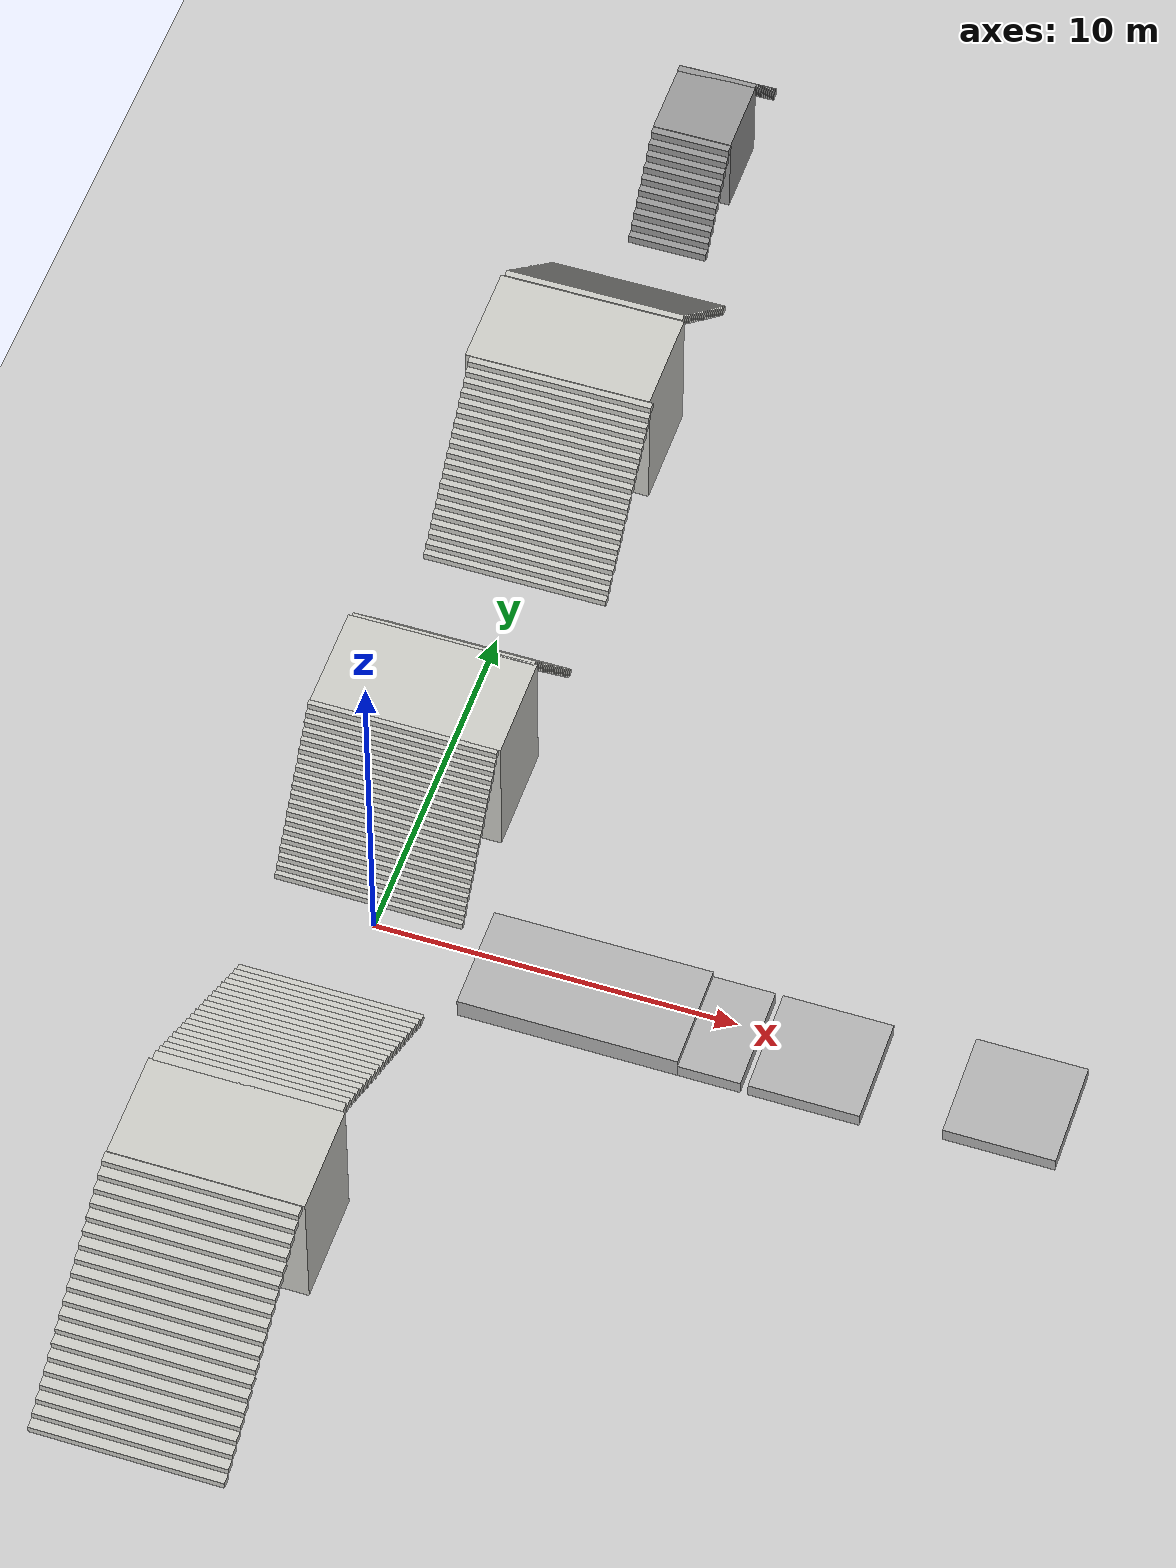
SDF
<?xml version="1.0" ?>
<sdf version="1.5">

  <world name="stairs_world">

    <physics type="ode">

      <max_step_size>0.001</max_step_size>

      <real_time_factor>1</real_time_factor>

      <real_time_update_rate>1000</real_time_update_rate>

      <gravity>0 0 -9.81</gravity>

    </physics>

    <scene>

      <ambient>0.4 0.4 0.4 1</ambient>

      <background>0.7 0.7 0.7 1</background>

    </scene>

    <include>

      <uri>model://sun</uri>

    </include>

    <include>

      <uri>model://ground_plane</uri>

    </include>

    <model name="stairs_20x30">
      <pose>0 -8 0 0 0 0</pose>
      <link name="Stairs_2">
        <pose>0 2.8 0 0 -0 0</pose>
        <visual name="Stairs_2_Visual_0">
          <pose>-0.312063 2.64146 0.1 0 -0 0</pose>
          <geometry>
            <box>
              <size>5.09 0.3 0.2</size>
            </box>
          </geometry>
          <material>
            <script>
              <uri>file://media/materials/scripts/gazebo.material</uri>
              <name>Gazebo/CeilingTiled</name>
            </script>
            <ambient>0.996078 0.47451 0.0196078 1</ambient>
          </material>
          <meta>
            <layer>0</layer>
          </meta>
        </visual>
        <collision name="Stairs_2_Collision_0">
          <geometry>
            <box>
              <size>5.09 0.3 0.2</size>
            </box>
          </geometry>
          <pose>-0.312063 2.64146 0.1 0 -0 0</pose>
        </collision>

        <visual name="Stairs_2_Visual_1">
          <pose>-0.312063 2.34146 0.3 0 -0 0</pose>
          <geometry>
            <box>
              <size>5.09 0.3 0.2</size>
            </box>
          </geometry>
          <material>
            <script>
              <uri>file://media/materials/scripts/gazebo.material</uri>
              <name>Gazebo/CeilingTiled</name>
            </script>
            <ambient>0.996078 0.47451 0.0196078 1</ambient>
          </material>
          <meta>
            <layer>0</layer>
          </meta>
        </visual>
        <collision name="Stairs_2_Collision_1">
          <geometry>
            <box>
              <size>5.09 0.3 0.2</size>
            </box>
          </geometry>
          <pose>-0.312063 2.34146 0.3 0 -0 0</pose>
        </collision>

        <visual name="Stairs_2_Visual_2">

          <pose>-0.312063 2.04146 0.5 0 -0 0</pose>

          <geometry>

            <box>

              <size>5.09 0.3 0.2</size>

            </box>

          </geometry>

          <material>

            <script>

              <uri>file://media/materials/scripts/gazebo.material</uri>

              <name>Gazebo/CeilingTiled</name>

            </script>

            <ambient>0.996078 0.47451 0.0196078 1</ambient>

          </material>

          <meta>

            <layer>0</layer>

          </meta>

        </visual>

        <collision name="Stairs_2_Collision_2">

          <geometry>

            <box>

              <size>5.09 0.3 0.2</size>

            </box>

          </geometry>

          <pose>-0.312063 2.04146 0.5 0 -0 0</pose>

        </collision>

        <visual name="Stairs_2_Visual_3">

          <pose>-0.312063 1.74146 0.7 0 -0 0</pose>

          <geometry>

            <box>

              <size>5.09 0.3 0.2</size>

            </box>

          </geometry>

          <material>

            <script>

              <uri>file://media/materials/scripts/gazebo.material</uri>

              <name>Gazebo/CeilingTiled</name>

            </script>

            <ambient>0.996078 0.47451 0.0196078 1</ambient>

          </material>

          <meta>

            <layer>0</layer>

          </meta>

        </visual>

        <collision name="Stairs_2_Collision_3">

          <geometry>

            <box>

              <size>5.09 0.3 0.2</size>

            </box>

          </geometry>

          <pose>-0.312063 1.74146 0.7 0 -0 0</pose>

        </collision>

        <visual name="Stairs_2_Visual_4">

          <pose>-0.312063 1.44146 0.9 0 -0 0</pose>

          <geometry>

            <box>

              <size>5.09 0.3 0.2</size>

            </box>

          </geometry>

          <material>

            <script>

              <uri>file://media/materials/scripts/gazebo.material</uri>

              <name>Gazebo/CeilingTiled</name>

            </script>

            <ambient>0.996078 0.47451 0.0196078 1</ambient>

          </material>

          <meta>

            <layer>0</layer>

          </meta>

        </visual>

        <collision name="Stairs_2_Collision_4">

          <geometry>

            <box>

              <size>5.09 0.3 0.2</size>

            </box>

          </geometry>

          <pose>-0.312063 1.44146 0.9 0 -0 0</pose>

        </collision>

        <visual name="Stairs_2_Visual_5">

          <pose>-0.312063 1.14146 1.1 0 -0 0</pose>

          <geometry>

            <box>

              <size>5.09 0.3 0.2</size>

            </box>

          </geometry>

          <material>

            <script>

              <uri>file://media/materials/scripts/gazebo.material</uri>

              <name>Gazebo/CeilingTiled</name>

            </script>

            <ambient>0.996078 0.47451 0.0196078 1</ambient>

          </material>

          <meta>

            <layer>0</layer>

          </meta>

        </visual>

        <collision name="Stairs_2_Collision_5">

          <geometry>

            <box>

              <size>5.09 0.3 0.2</size>

            </box>

          </geometry>

          <pose>-0.312063 1.14146 1.1 0 -0 0</pose>

        </collision>

        <visual name="Stairs_2_Visual_6">

          <pose>-0.312063 0.84146 1.3 0 -0 0</pose>

          <geometry>

            <box>

              <size>5.09 0.3 0.2</size>

            </box>

          </geometry>

          <material>

            <script>

              <uri>file://media/materials/scripts/gazebo.material</uri>

              <name>Gazebo/CeilingTiled</name>

            </script>

            <ambient>0.996078 0.47451 0.0196078 1</ambient>

          </material>

          <meta>

            <layer>0</layer>

          </meta>

        </visual>

        <collision name="Stairs_2_Collision_6">

          <geometry>

            <box>

              <size>5.09 0.3 0.2</size>

            </box>

          </geometry>

          <pose>-0.312063 0.84146 1.3 0 -0 0</pose>

        </collision>

        <visual name="Stairs_2_Visual_7">

          <pose>-0.312063 0.54146 1.5 0 -0 0</pose>

          <geometry>

            <box>

              <size>5.09 0.3 0.2</size>

            </box>

          </geometry>

          <material>

            <script>

              <uri>file://media/materials/scripts/gazebo.material</uri>

              <name>Gazebo/CeilingTiled</name>

            </script>

            <ambient>0.996078 0.47451 0.0196078 1</ambient>

          </material>

          <meta>

            <layer>0</layer>

          </meta>

        </visual>

        <collision name="Stairs_2_Collision_7">

          <geometry>

            <box>

              <size>5.09 0.3 0.2</size>

            </box>

          </geometry>

          <pose>-0.312063 0.54146 1.5 0 -0 0</pose>

        </collision>

        <visual name="Stairs_2_Visual_8">

          <pose>-0.312063 0.24146 1.7 0 -0 0</pose>

          <geometry>

            <box>

              <size>5.09 0.3 0.2</size>

            </box>

          </geometry>

          <material>

            <script>

              <uri>file://media/materials/scripts/gazebo.material</uri>

              <name>Gazebo/CeilingTiled</name>

            </script>

            <ambient>0.996078 0.47451 0.0196078 1</ambient>

          </material>

          <meta>

            <layer>0</layer>

          </meta>

        </visual>

        <collision name="Stairs_2_Collision_8">

          <geometry>

            <box>

              <size>5.09 0.3 0.2</size>

            </box>

          </geometry>

          <pose>-0.312063 0.24146 1.7 0 -0 0</pose>

        </collision>

        <visual name="Stairs_2_Visual_9">

          <pose>-0.312063 -0.05854 1.9 0 -0 0</pose>

          <geometry>

            <box>

              <size>5.09 0.3 0.2</size>

            </box>

          </geometry>

          <material>

            <script>

              <uri>file://media/materials/scripts/gazebo.material</uri>

              <name>Gazebo/CeilingTiled</name>

            </script>

            <ambient>0.996078 0.47451 0.0196078 1</ambient>

          </material>

          <meta>

            <layer>0</layer>

          </meta>

        </visual>

        <collision name="Stairs_2_Collision_9">

          <geometry>

            <box>

              <size>5.09 0.3 0.2</size>

            </box>

          </geometry>

          <pose>-0.312063 -0.05854 1.9 0 -0 0</pose>

        </collision>

        <visual name="Stairs_2_Visual_10">

          <pose>-0.312063 -0.35854 2.1 0 -0 0</pose>

          <geometry>

            <box>

              <size>5.09 0.3 0.2</size>

            </box>

          </geometry>

          <material>

            <script>

              <uri>file://media/materials/scripts/gazebo.material</uri>

              <name>Gazebo/CeilingTiled</name>

            </script>

            <ambient>0.996078 0.47451 0.0196078 1</ambient>

          </material>

          <meta>

            <layer>0</layer>

          </meta>

        </visual>

        <collision name="Stairs_2_Collision_10">

          <geometry>

            <box>

              <size>5.09 0.3 0.2</size>

            </box>

          </geometry>

          <pose>-0.312063 -0.35854 2.1 0 -0 0</pose>

        </collision>

        <visual name="Stairs_2_Visual_11">

          <pose>-0.312063 -0.65854 2.3 0 -0 0</pose>

          <geometry>

            <box>

              <size>5.09 0.3 0.2</size>

            </box>

          </geometry>

          <material>

            <script>

              <uri>file://media/materials/scripts/gazebo.material</uri>

              <name>Gazebo/CeilingTiled</name>

            </script>

            <ambient>0.996078 0.47451 0.0196078 1</ambient>

          </material>

          <meta>

            <layer>0</layer>

          </meta>

        </visual>

        <collision name="Stairs_2_Collision_11">

          <geometry>

            <box>

              <size>5.09 0.3 0.2</size>

            </box>

          </geometry>

          <pose>-0.312063 -0.65854 2.3 0 -0 0</pose>

        </collision>

        <visual name="Stairs_2_Visual_12">

          <pose>-0.312063 -0.95854 2.5 0 -0 0</pose>

          <geometry>

            <box>

              <size>5.09 0.3 0.2</size>

            </box>

          </geometry>

          <material>

            <script>

              <uri>file://media/materials/scripts/gazebo.material</uri>

              <name>Gazebo/CeilingTiled</name>

            </script>

            <ambient>0.996078 0.47451 0.0196078 1</ambient>

          </material>

          <meta>

            <layer>0</layer>

          </meta>

        </visual>

        <collision name="Stairs_2_Collision_12">

          <geometry>

            <box>

              <size>5.09 0.3 0.2</size>

            </box>

          </geometry>

          <pose>-0.312063 -0.95854 2.5 0 -0 0</pose>

        </collision>

        <visual name="Stairs_2_Visual_13">

          <pose>-0.312063 -1.25854 2.7 0 -0 0</pose>

          <geometry>

            <box>

              <size>5.09 0.3 0.2</size>

            </box>

          </geometry>

          <material>

            <script>

              <uri>file://media/materials/scripts/gazebo.material</uri>

              <name>Gazebo/CeilingTiled</name>

            </script>

            <ambient>0.996078 0.47451 0.0196078 1</ambient>

          </material>

          <meta>

            <layer>0</layer>

          </meta>

        </visual>

        <collision name="Stairs_2_Collision_13">

          <geometry>

            <box>

              <size>5.09 0.3 0.2</size>

            </box>

          </geometry>

          <pose>-0.312063 -1.25854 2.7 0 -0 0</pose>

        </collision>

        <visual name="Stairs_2_Visual_14">

          <pose>-0.312063 -1.55854 2.9 0 -0 0</pose>

          <geometry>

            <box>

              <size>5.09 0.3 0.2</size>

            </box>

          </geometry>

          <material>

            <script>

              <uri>file://media/materials/scripts/gazebo.material</uri>

              <name>Gazebo/CeilingTiled</name>

            </script>

            <ambient>0.996078 0.47451 0.0196078 1</ambient>

          </material>

          <meta>

            <layer>0</layer>

          </meta>

        </visual>

        <collision name="Stairs_2_Collision_14">

          <geometry>

            <box>

              <size>5.09 0.3 0.2</size>

            </box>

          </geometry>

          <pose>-0.312063 -1.55854 2.9 0 -0 0</pose>

        </collision>

        <visual name="Stairs_2_Visual_15">

          <pose>-0.312063 -1.85854 3.1 0 -0 0</pose>

          <geometry>

            <box>

              <size>5.09 0.3 0.2</size>

            </box>

          </geometry>

          <material>

            <script>

              <uri>file://media/materials/scripts/gazebo.material</uri>

              <name>Gazebo/CeilingTiled</name>

            </script>

            <ambient>0.996078 0.47451 0.0196078 1</ambient>

          </material>

          <meta>

            <layer>0</layer>

          </meta>

        </visual>

        <collision name="Stairs_2_Collision_15">

          <geometry>

            <box>

              <size>5.09 0.3 0.2</size>

            </box>

          </geometry>

          <pose>-0.312063 -1.85854 3.1 0 -0 0</pose>

        </collision>

        <visual name="Stairs_2_Visual_16">

          <pose>-0.312063 -2.15854 3.3 0 -0 0</pose>

          <geometry>

            <box>

              <size>5.09 0.3 0.2</size>

            </box>

          </geometry>

          <material>

            <script>

              <uri>file://media/materials/scripts/gazebo.material</uri>

              <name>Gazebo/CeilingTiled</name>

            </script>

            <ambient>0.996078 0.47451 0.0196078 1</ambient>

          </material>

          <meta>

            <layer>0</layer>

          </meta>

        </visual>

        <collision name="Stairs_2_Collision_16">

          <geometry>

            <box>

              <size>5.09 0.3 0.2</size>

            </box>

          </geometry>

          <pose>-0.312063 -2.15854 3.3 0 -0 0</pose>

        </collision>

        <visual name="Stairs_2_Visual_17">

          <pose>-0.312063 -2.45854 3.5 0 -0 0</pose>

          <geometry>

            <box>

              <size>5.09 0.3 0.2</size>

            </box>

          </geometry>

          <material>

            <script>

              <uri>file://media/materials/scripts/gazebo.material</uri>

              <name>Gazebo/CeilingTiled</name>

            </script>

            <ambient>0.996078 0.47451 0.0196078 1</ambient>

          </material>

          <meta>

            <layer>0</layer>

          </meta>

        </visual>

        <collision name="Stairs_2_Collision_17">

          <geometry>

            <box>

              <size>5.09 0.3 0.2</size>

            </box>

          </geometry>

          <pose>-0.312063 -2.45854 3.5 0 -0 0</pose>

        </collision>

        <visual name="Stairs_2_Visual_18">

          <pose>-0.312063 -2.75854 3.7 0 -0 0</pose>

          <geometry>

            <box>

              <size>5.09 0.3 0.2</size>

            </box>

          </geometry>

          <material>

            <script>

              <uri>file://media/materials/scripts/gazebo.material</uri>

              <name>Gazebo/CeilingTiled</name>

            </script>

            <ambient>0.996078 0.47451 0.0196078 1</ambient>

          </material>

          <meta>

            <layer>0</layer>

          </meta>

        </visual>

        <collision name="Stairs_2_Collision_18">

          <geometry>

            <box>

              <size>5.09 0.3 0.2</size>

            </box>

          </geometry>

          <pose>-0.312063 -2.75854 3.7 0 -0 0</pose>

        </collision>

        <visual name="Stairs_2_Visual_19">

          <pose>-0.312063 -3.05854 3.9 0 -0 0</pose>

          <geometry>

            <box>

              <size>5.09 0.3 0.2</size>

            </box>

          </geometry>

          <material>

            <script>

              <uri>file://media/materials/scripts/gazebo.material</uri>

              <name>Gazebo/CeilingTiled</name>

            </script>

            <ambient>0.996078 0.47451 0.0196078 1</ambient>

          </material>

          <meta>

            <layer>0</layer>

          </meta>

        </visual>

        <collision name="Stairs_2_Collision_19">

          <geometry>

            <box>

              <size>5.09 0.3 0.2</size>

            </box>

          </geometry>

          <pose>-0.312063 -3.05854 3.9 0 -0 0</pose>

        </collision>

      </link>

      <link name="Stairs_4">
        <pose>0 -2.8 0 0 -0 0</pose>

        <visual name="Stairs_4_Visual_0">

          <pose>-0.367728 -6.44772 0.1 0 -0 -3.14159</pose>

          <geometry>

            <box>

              <size>5.21 0.3 0.2</size>

            </box>

          </geometry>

          <material>

            <script>

              <uri>file://media/materials/scripts/gazebo.material</uri>

              <name>Gazebo/CeilingTiled</name>

            </script>

            <ambient>0.996078 0.47451 0.0196078 1</ambient>

          </material>

          <meta>

            <layer>0</layer>

          </meta>

        </visual>

        <collision name="Stairs_4_Collision_0">

          <geometry>

            <box>

              <size>5.21 0.3 0.2</size>

            </box>

          </geometry>

          <pose>-0.367728 -6.44772 0.1 0 -0 -3.14159</pose>

        </collision>

        <visual name="Stairs_4_Visual_1">

          <pose>-0.367728 -6.14772 0.3 0 -0 -3.14159</pose>

          <geometry>

            <box>

              <size>5.21 0.3 0.2</size>

            </box>

          </geometry>

          <material>

            <script>

              <uri>file://media/materials/scripts/gazebo.material</uri>

              <name>Gazebo/CeilingTiled</name>

            </script>

            <ambient>0.996078 0.47451 0.0196078 1</ambient>

          </material>

          <meta>

            <layer>0</layer>

          </meta>

        </visual>

        <collision name="Stairs_4_Collision_1">

          <geometry>

            <box>

              <size>5.21 0.3 0.2</size>

            </box>

          </geometry>

          <pose>-0.367728 -6.14772 0.3 0 -0 -3.14159</pose>

        </collision>

        <visual name="Stairs_4_Visual_2">

          <pose>-0.367728 -5.84772 0.5 0 -0 -3.14159</pose>

          <geometry>

            <box>

              <size>5.21 0.3 0.2</size>

            </box>

          </geometry>

          <material>

            <script>

              <uri>file://media/materials/scripts/gazebo.material</uri>

              <name>Gazebo/CeilingTiled</name>

            </script>

            <ambient>0.996078 0.47451 0.0196078 1</ambient>

          </material>

          <meta>

            <layer>0</layer>

          </meta>

        </visual>

        <collision name="Stairs_4_Collision_2">

          <geometry>

            <box>

              <size>5.21 0.3 0.2</size>

            </box>

          </geometry>

          <pose>-0.367728 -5.84772 0.5 0 -0 -3.14159</pose>

        </collision>

        <visual name="Stairs_4_Visual_3">

          <pose>-0.367728 -5.54772 0.7 0 -0 -3.14159</pose>

          <geometry>

            <box>

              <size>5.21 0.3 0.2</size>

            </box>

          </geometry>

          <material>

            <script>

              <uri>file://media/materials/scripts/gazebo.material</uri>

              <name>Gazebo/CeilingTiled</name>

            </script>

            <ambient>0.996078 0.47451 0.0196078 1</ambient>

          </material>

          <meta>

            <layer>0</layer>

          </meta>

        </visual>

        <collision name="Stairs_4_Collision_3">

          <geometry>

            <box>

              <size>5.21 0.3 0.2</size>

            </box>

          </geometry>

          <pose>-0.367728 -5.54772 0.7 0 -0 -3.14159</pose>

        </collision>

        <visual name="Stairs_4_Visual_4">

          <pose>-0.367728 -5.24772 0.9 0 -0 -3.14159</pose>

          <geometry>

            <box>

              <size>5.21 0.3 0.2</size>

            </box>

          </geometry>

          <material>

            <script>

              <uri>file://media/materials/scripts/gazebo.material</uri>

              <name>Gazebo/CeilingTiled</name>

            </script>

            <ambient>0.996078 0.47451 0.0196078 1</ambient>

          </material>

          <meta>

            <layer>0</layer>

          </meta>

        </visual>

        <collision name="Stairs_4_Collision_4">

          <geometry>

            <box>

              <size>5.21 0.3 0.2</size>

            </box>

          </geometry>

          <pose>-0.367728 -5.24772 0.9 0 -0 -3.14159</pose>

        </collision>

        <visual name="Stairs_4_Visual_5">

          <pose>-0.367728 -4.94772 1.1 0 -0 -3.14159</pose>

          <geometry>

            <box>

              <size>5.21 0.3 0.2</size>

            </box>

          </geometry>

          <material>

            <script>

              <uri>file://media/materials/scripts/gazebo.material</uri>

              <name>Gazebo/CeilingTiled</name>

            </script>

            <ambient>0.996078 0.47451 0.0196078 1</ambient>

          </material>

          <meta>

            <layer>0</layer>

          </meta>

        </visual>

        <collision name="Stairs_4_Collision_5">

          <geometry>

            <box>

              <size>5.21 0.3 0.2</size>

            </box>

          </geometry>

          <pose>-0.367728 -4.94772 1.1 0 -0 -3.14159</pose>

        </collision>

        <visual name="Stairs_4_Visual_6">

          <pose>-0.367728 -4.64772 1.3 0 -0 -3.14159</pose>

          <geometry>

            <box>

              <size>5.21 0.3 0.2</size>

            </box>

          </geometry>

          <material>

            <script>

              <uri>file://media/materials/scripts/gazebo.material</uri>

              <name>Gazebo/CeilingTiled</name>

            </script>

            <ambient>0.996078 0.47451 0.0196078 1</ambient>

          </material>

          <meta>

            <layer>0</layer>

          </meta>

        </visual>

        <collision name="Stairs_4_Collision_6">

          <geometry>

            <box>

              <size>5.21 0.3 0.2</size>

            </box>

          </geometry>

          <pose>-0.367728 -4.64772 1.3 0 -0 -3.14159</pose>

        </collision>

        <visual name="Stairs_4_Visual_7">

          <pose>-0.367728 -4.34772 1.5 0 -0 -3.14159</pose>

          <geometry>

            <box>

              <size>5.21 0.3 0.2</size>

            </box>

          </geometry>

          <material>

            <script>

              <uri>file://media/materials/scripts/gazebo.material</uri>

              <name>Gazebo/CeilingTiled</name>

            </script>

            <ambient>0.996078 0.47451 0.0196078 1</ambient>

          </material>

          <meta>

            <layer>0</layer>

          </meta>

        </visual>

        <collision name="Stairs_4_Collision_7">

          <geometry>

            <box>

              <size>5.21 0.3 0.2</size>

            </box>

          </geometry>

          <pose>-0.367728 -4.34772 1.5 0 -0 -3.14159</pose>

        </collision>

        <visual name="Stairs_4_Visual_8">

          <pose>-0.367728 -4.04772 1.7 0 -0 -3.14159</pose>

          <geometry>

            <box>

              <size>5.21 0.3 0.2</size>

            </box>

          </geometry>

          <material>

            <script>

              <uri>file://media/materials/scripts/gazebo.material</uri>

              <name>Gazebo/CeilingTiled</name>

            </script>

            <ambient>0.996078 0.47451 0.0196078 1</ambient>

          </material>

          <meta>

            <layer>0</layer>

          </meta>

        </visual>

        <collision name="Stairs_4_Collision_8">

          <geometry>

            <box>

              <size>5.21 0.3 0.2</size>

            </box>

          </geometry>

          <pose>-0.367728 -4.04772 1.7 0 -0 -3.14159</pose>

        </collision>

        <visual name="Stairs_4_Visual_9">

          <pose>-0.367728 -3.74772 1.9 0 -0 -3.14159</pose>

          <geometry>

            <box>

              <size>5.21 0.3 0.2</size>

            </box>

          </geometry>

          <material>

            <script>

              <uri>file://media/materials/scripts/gazebo.material</uri>

              <name>Gazebo/CeilingTiled</name>

            </script>

            <ambient>0.996078 0.47451 0.0196078 1</ambient>

          </material>

          <meta>

            <layer>0</layer>

          </meta>

        </visual>

        <collision name="Stairs_4_Collision_9">

          <geometry>

            <box>

              <size>5.21 0.3 0.2</size>

            </box>

          </geometry>

          <pose>-0.367728 -3.74772 1.9 0 -0 -3.14159</pose>

        </collision>

        <visual name="Stairs_4_Visual_10">

          <pose>-0.367728 -3.44772 2.1 0 -0 -3.14159</pose>

          <geometry>

            <box>

              <size>5.21 0.3 0.2</size>

            </box>

          </geometry>

          <material>

            <script>

              <uri>file://media/materials/scripts/gazebo.material</uri>

              <name>Gazebo/CeilingTiled</name>

            </script>

            <ambient>0.996078 0.47451 0.0196078 1</ambient>

          </material>

          <meta>

            <layer>0</layer>

          </meta>

        </visual>

        <collision name="Stairs_4_Collision_10">

          <geometry>

            <box>

              <size>5.21 0.3 0.2</size>

            </box>

          </geometry>

          <pose>-0.367728 -3.44772 2.1 0 -0 -3.14159</pose>

        </collision>

        <visual name="Stairs_4_Visual_11">

          <pose>-0.367728 -3.14772 2.3 0 -0 -3.14159</pose>

          <geometry>

            <box>

              <size>5.21 0.3 0.2</size>

            </box>

          </geometry>

          <material>

            <script>

              <uri>file://media/materials/scripts/gazebo.material</uri>

              <name>Gazebo/CeilingTiled</name>

            </script>

            <ambient>0.996078 0.47451 0.0196078 1</ambient>

          </material>

          <meta>

            <layer>0</layer>

          </meta>

        </visual>

        <collision name="Stairs_4_Collision_11">

          <geometry>

            <box>

              <size>5.21 0.3 0.2</size>

            </box>

          </geometry>

          <pose>-0.367728 -3.14772 2.3 0 -0 -3.14159</pose>

        </collision>

        <visual name="Stairs_4_Visual_12">

          <pose>-0.367728 -2.84772 2.5 0 -0 -3.14159</pose>

          <geometry>

            <box>

              <size>5.21 0.3 0.2</size>

            </box>

          </geometry>

          <material>

            <script>

              <uri>file://media/materials/scripts/gazebo.material</uri>

              <name>Gazebo/CeilingTiled</name>

            </script>

            <ambient>0.996078 0.47451 0.0196078 1</ambient>

          </material>

          <meta>

            <layer>0</layer>

          </meta>

        </visual>

        <collision name="Stairs_4_Collision_12">

          <geometry>

            <box>

              <size>5.21 0.3 0.2</size>

            </box>

          </geometry>

          <pose>-0.367728 -2.84772 2.5 0 -0 -3.14159</pose>

        </collision>

        <visual name="Stairs_4_Visual_13">

          <pose>-0.367728 -2.54772 2.7 0 -0 -3.14159</pose>

          <geometry>

            <box>

              <size>5.21 0.3 0.2</size>

            </box>

          </geometry>

          <material>

            <script>

              <uri>file://media/materials/scripts/gazebo.material</uri>

              <name>Gazebo/CeilingTiled</name>

            </script>

            <ambient>0.996078 0.47451 0.0196078 1</ambient>

          </material>

          <meta>

            <layer>0</layer>

          </meta>

        </visual>

        <collision name="Stairs_4_Collision_13">

          <geometry>

            <box>

              <size>5.21 0.3 0.2</size>

            </box>

          </geometry>

          <pose>-0.367728 -2.54772 2.7 0 -0 -3.14159</pose>

        </collision>

        <visual name="Stairs_4_Visual_14">

          <pose>-0.367728 -2.24772 2.9 0 -0 -3.14159</pose>

          <geometry>

            <box>

              <size>5.21 0.3 0.2</size>

            </box>

          </geometry>

          <material>

            <script>

              <uri>file://media/materials/scripts/gazebo.material</uri>

              <name>Gazebo/CeilingTiled</name>

            </script>

            <ambient>0.996078 0.47451 0.0196078 1</ambient>

          </material>

          <meta>

            <layer>0</layer>

          </meta>

        </visual>

        <collision name="Stairs_4_Collision_14">

          <geometry>

            <box>

              <size>5.21 0.3 0.2</size>

            </box>

          </geometry>

          <pose>-0.367728 -2.24772 2.9 0 -0 -3.14159</pose>

        </collision>

        <visual name="Stairs_4_Visual_15">

          <pose>-0.367728 -1.94772 3.1 0 -0 -3.14159</pose>

          <geometry>

            <box>

              <size>5.21 0.3 0.2</size>

            </box>

          </geometry>

          <material>

            <script>

              <uri>file://media/materials/scripts/gazebo.material</uri>

              <name>Gazebo/CeilingTiled</name>

            </script>

            <ambient>0.996078 0.47451 0.0196078 1</ambient>

          </material>

          <meta>

            <layer>0</layer>

          </meta>

        </visual>

        <collision name="Stairs_4_Collision_15">

          <geometry>

            <box>

              <size>5.21 0.3 0.2</size>

            </box>

          </geometry>

          <pose>-0.367728 -1.94772 3.1 0 -0 -3.14159</pose>

        </collision>

        <visual name="Stairs_4_Visual_16">

          <pose>-0.367728 -1.64772 3.3 0 -0 -3.14159</pose>

          <geometry>

            <box>

              <size>5.21 0.3 0.2</size>

            </box>

          </geometry>

          <material>

            <script>

              <uri>file://media/materials/scripts/gazebo.material</uri>

              <name>Gazebo/CeilingTiled</name>

            </script>

            <ambient>0.996078 0.47451 0.0196078 1</ambient>

          </material>

          <meta>

            <layer>0</layer>

          </meta>

        </visual>

        <collision name="Stairs_4_Collision_16">

          <geometry>

            <box>

              <size>5.21 0.3 0.2</size>

            </box>

          </geometry>

          <pose>-0.367728 -1.64772 3.3 0 -0 -3.14159</pose>

        </collision>

        <visual name="Stairs_4_Visual_17">

          <pose>-0.367728 -1.34772 3.5 0 -0 -3.14159</pose>

          <geometry>

            <box>

              <size>5.21 0.3 0.2</size>

            </box>

          </geometry>

          <material>

            <script>

              <uri>file://media/materials/scripts/gazebo.material</uri>

              <name>Gazebo/CeilingTiled</name>

            </script>

            <ambient>0.996078 0.47451 0.0196078 1</ambient>

          </material>

          <meta>

            <layer>0</layer>

          </meta>

        </visual>

        <collision name="Stairs_4_Collision_17">

          <geometry>

            <box>

              <size>5.21 0.3 0.2</size>

            </box>

          </geometry>

          <pose>-0.367728 -1.34772 3.5 0 -0 -3.14159</pose>

        </collision>

        <visual name="Stairs_4_Visual_18">

          <pose>-0.367728 -1.04772 3.7 0 -0 -3.14159</pose>

          <geometry>

            <box>

              <size>5.21 0.3 0.2</size>

            </box>

          </geometry>

          <material>

            <script>

              <uri>file://media/materials/scripts/gazebo.material</uri>

              <name>Gazebo/CeilingTiled</name>

            </script>

            <ambient>0.996078 0.47451 0.0196078 1</ambient>

          </material>

          <meta>

            <layer>0</layer>

          </meta>

        </visual>

        <collision name="Stairs_4_Collision_18">

          <geometry>

            <box>

              <size>5.21 0.3 0.2</size>

            </box>

          </geometry>

          <pose>-0.367728 -1.04772 3.7 0 -0 -3.14159</pose>

        </collision>

        <visual name="Stairs_4_Visual_19">

          <pose>-0.367728 -0.74772 3.9 0 -0 -3.14159</pose>

          <geometry>

            <box>

              <size>5.21 0.3 0.2</size>

            </box>

          </geometry>

          <material>

            <script>

              <uri>file://media/materials/scripts/gazebo.material</uri>

              <name>Gazebo/CeilingTiled</name>

            </script>

            <ambient>0.996078 0.47451 0.0196078 1</ambient>

          </material>

          <meta>

            <layer>0</layer>

          </meta>

        </visual>

        <collision name="Stairs_4_Collision_19">

          <geometry>

            <box>

              <size>5.21 0.3 0.2</size>

            </box>

          </geometry>

          <pose>-0.367728 -0.74772 3.9 0 -0 -3.14159</pose>

        </collision>

      </link>

      <link name="Wall_0">

        <collision name="Wall_0_Collision">

          <geometry>

            <box>

              <size>5.25 3 4</size>

            </box>

          </geometry>

          <pose>0 0 2 0 -0 0</pose>

        </collision>

        <visual name="Wall_0_Visual">

          <pose>0 0 2 0 -0 0</pose>

          <geometry>

            <box>

              <size>5.25 3 4</size>

            </box>

          </geometry>

          <material>

            <script>

              <uri>file://media/materials/scripts/gazebo.material</uri>

              <name>Gazebo/CeilingTiled</name>

            </script>

            <ambient>0.760784 0.662745 0.627451 1</ambient>

          </material>

          <meta>

            <layer>0</layer>

          </meta>

        </visual>

        <pose>-0.327481 -1.88249 0 0 -0 0</pose>

      </link>

      <static>1</static>

    </model>

    <model name="stairs_20x15">
      <pose>0 7 0 0 0 0</pose>
      <link name="Stairs_2">
        <pose>0 -0.15 0 0 -0 0</pose>
        <visual name="Stairs_2_Visual_0">
          <pose>-0.312063 2.64146 0.1 0 -0 0</pose>
          <geometry>
            <box>
              <size>5.09 0.15 0.2</size>
            </box>
          </geometry>
          <material>
            <script>
              <uri>file://media/materials/scripts/gazebo.material</uri>
              <name>Gazebo/CeilingTiled</name>
            </script>
            <ambient>0.996078 0.47451 0.0196078 1</ambient>
          </material>
          <meta>
            <layer>0</layer>
          </meta>
        </visual>
        <collision name="Stairs_2_Collision_0">
          <geometry>
            <box>
              <size>5.09 0.15 0.2</size>
            </box>
          </geometry>
          <pose>-0.312063 2.64146 0.1 0 -0 0</pose>
        </collision>

        <visual name="Stairs_2_Visual_1">
          <pose>-0.312063 2.49146 0.3 0 -0 0</pose>
          <geometry>
            <box>
              <size>5.09 0.15 0.2</size>
            </box>
          </geometry>
          <material>
            <script>
              <uri>file://media/materials/scripts/gazebo.material</uri>
              <name>Gazebo/CeilingTiled</name>
            </script>
            <ambient>0.996078 0.47451 0.0196078 1</ambient>
          </material>
          <meta>
            <layer>0</layer>
          </meta>
        </visual>
        <collision name="Stairs_2_Collision_1">
          <geometry>
            <box>
              <size>5.09 0.15 0.2</size>
            </box>
          </geometry>
          <pose>-0.312063 2.49146 0.3 0 -0 0</pose>
        </collision>
        <visual name="Stairs_2_Visual_2">
          <pose>-0.312063 2.34146 0.5 0 -0 0</pose>
          <geometry>
            <box>
              <size>5.09 0.15 0.2</size>
            </box>
          </geometry>
          <material>
            <script>
              <uri>file://media/materials/scripts/gazebo.material</uri>
              <name>Gazebo/CeilingTiled</name>
            </script>
            <ambient>0.996078 0.47451 0.0196078 1</ambient>
          </material>
          <meta>
            <layer>0</layer>
          </meta>
        </visual>
        <collision name="Stairs_2_Collision_2">
          <geometry>

            <box>

              <size>5.09 0.15 0.2</size>

            </box>

          </geometry>

          <pose>-0.312063 2.34146 0.5 0 -0 0</pose>

        </collision>

        <visual name="Stairs_2_Visual_3">

          <pose>-0.312063 2.19146 0.7 0 -0 0</pose>

          <geometry>

            <box>

              <size>5.09 0.15 0.2</size>

            </box>

          </geometry>

          <material>

            <script>

              <uri>file://media/materials/scripts/gazebo.material</uri>

              <name>Gazebo/CeilingTiled</name>

            </script>

            <ambient>0.996078 0.47451 0.0196078 1</ambient>

          </material>

          <meta>

            <layer>0</layer>

          </meta>

        </visual>

        <collision name="Stairs_2_Collision_3">

          <geometry>

            <box>

              <size>5.09 0.15 0.2</size>

            </box>

          </geometry>

          <pose>-0.312063 2.19146 0.7 0 -0 0</pose>

        </collision>

        <visual name="Stairs_2_Visual_4">

          <pose>-0.312063 2.04146 0.9 0 -0 0</pose>

          <geometry>

            <box>

              <size>5.09 0.15 0.2</size>

            </box>

          </geometry>

          <material>

            <script>

              <uri>file://media/materials/scripts/gazebo.material</uri>

              <name>Gazebo/CeilingTiled</name>

            </script>

            <ambient>0.996078 0.47451 0.0196078 1</ambient>

          </material>

          <meta>

            <layer>0</layer>

          </meta>

        </visual>

        <collision name="Stairs_2_Collision_4">

          <geometry>

            <box>

              <size>5.09 0.15 0.2</size>

            </box>

          </geometry>

          <pose>-0.312063 2.04146 0.9 0 -0 0</pose>

        </collision>

        <visual name="Stairs_2_Visual_5">

          <pose>-0.312063 1.89146 1.1 0 -0 0</pose>

          <geometry>

            <box>

              <size>5.09 0.15 0.2</size>

            </box>

          </geometry>

          <material>

            <script>

              <uri>file://media/materials/scripts/gazebo.material</uri>

              <name>Gazebo/CeilingTiled</name>

            </script>

            <ambient>0.996078 0.47451 0.0196078 1</ambient>

          </material>

          <meta>

            <layer>0</layer>

          </meta>

        </visual>

        <collision name="Stairs_2_Collision_5">

          <geometry>

            <box>

              <size>5.09 0.15 0.2</size>

            </box>

          </geometry>

          <pose>-0.312063 1.89146 1.1 0 -0 0</pose>

        </collision>

        <visual name="Stairs_2_Visual_6">

          <pose>-0.312063 1.74146 1.3 0 -0 0</pose>

          <geometry>

            <box>

              <size>5.09 0.15 0.2</size>

            </box>

          </geometry>

          <material>

            <script>

              <uri>file://media/materials/scripts/gazebo.material</uri>

              <name>Gazebo/CeilingTiled</name>

            </script>

            <ambient>0.996078 0.47451 0.0196078 1</ambient>

          </material>

          <meta>

            <layer>0</layer>

          </meta>

        </visual>

        <collision name="Stairs_2_Collision_6">

          <geometry>

            <box>

              <size>5.09 0.15 0.2</size>

            </box>

          </geometry>

          <pose>-0.312063 1.74146 1.3 0 -0 0</pose>

        </collision>

        <visual name="Stairs_2_Visual_7">

          <pose>-0.312063 1.59146 1.5 0 -0 0</pose>

          <geometry>

            <box>

              <size>5.09 0.15 0.2</size>

            </box>

          </geometry>

          <material>

            <script>

              <uri>file://media/materials/scripts/gazebo.material</uri>

              <name>Gazebo/CeilingTiled</name>

            </script>

            <ambient>0.996078 0.47451 0.0196078 1</ambient>

          </material>

          <meta>

            <layer>0</layer>

          </meta>

        </visual>

        <collision name="Stairs_2_Collision_7">

          <geometry>

            <box>

              <size>5.09 0.15 0.2</size>

            </box>

          </geometry>

          <pose>-0.312063 1.59146 1.5 0 -0 0</pose>

        </collision>

        <visual name="Stairs_2_Visual_8">

          <pose>-0.312063 1.44146 1.7 0 -0 0</pose>

          <geometry>

            <box>

              <size>5.09 0.15 0.2</size>

            </box>

          </geometry>

          <material>

            <script>

              <uri>file://media/materials/scripts/gazebo.material</uri>

              <name>Gazebo/CeilingTiled</name>

            </script>

            <ambient>0.996078 0.47451 0.0196078 1</ambient>

          </material>

          <meta>

            <layer>0</layer>

          </meta>

        </visual>

        <collision name="Stairs_2_Collision_8">

          <geometry>

            <box>

              <size>5.09 0.15 0.2</size>

            </box>

          </geometry>

          <pose>-0.312063 1.44146 1.7 0 -0 0</pose>

        </collision>

        <visual name="Stairs_2_Visual_9">

          <pose>-0.312063 1.29146 1.9 0 -0 0</pose>

          <geometry>

            <box>

              <size>5.09 0.15 0.2</size>

            </box>

          </geometry>

          <material>

            <script>

              <uri>file://media/materials/scripts/gazebo.material</uri>

              <name>Gazebo/CeilingTiled</name>

            </script>

            <ambient>0.996078 0.47451 0.0196078 1</ambient>

          </material>

          <meta>

            <layer>0</layer>

          </meta>

        </visual>

        <collision name="Stairs_2_Collision_9">

          <geometry>

            <box>

              <size>5.09 0.15 0.2</size>

            </box>

          </geometry>

          <pose>-0.312063 1.29146 1.9 0 -0 0</pose>

        </collision>

        <visual name="Stairs_2_Visual_10">

          <pose>-0.312063 1.14146 2.1 0 -0 0</pose>

          <geometry>

            <box>

              <size>5.09 0.15 0.2</size>

            </box>

          </geometry>

          <material>

            <script>

              <uri>file://media/materials/scripts/gazebo.material</uri>

              <name>Gazebo/CeilingTiled</name>

            </script>

            <ambient>0.996078 0.47451 0.0196078 1</ambient>

          </material>

          <meta>

            <layer>0</layer>

          </meta>

        </visual>

        <collision name="Stairs_2_Collision_10">

          <geometry>

            <box>

              <size>5.09 0.15 0.2</size>

            </box>

          </geometry>

          <pose>-0.312063 1.14146 2.1 0 -0 0</pose>

        </collision>

        <visual name="Stairs_2_Visual_11">

          <pose>-0.312063 0.99146 2.3 0 -0 0</pose>

          <geometry>

            <box>

              <size>5.09 0.15 0.2</size>

            </box>

          </geometry>

          <material>

            <script>

              <uri>file://media/materials/scripts/gazebo.material</uri>

              <name>Gazebo/CeilingTiled</name>

            </script>

            <ambient>0.996078 0.47451 0.0196078 1</ambient>

          </material>

          <meta>

            <layer>0</layer>

          </meta>

        </visual>

        <collision name="Stairs_2_Collision_11">

          <geometry>

            <box>

              <size>5.09 0.15 0.2</size>

            </box>

          </geometry>

          <pose>-0.312063 0.99146 2.3 0 -0 0</pose>

        </collision>

        <visual name="Stairs_2_Visual_12">

          <pose>-0.312063 0.84146 2.5 0 -0 0</pose>

          <geometry>

            <box>

              <size>5.09 0.15 0.2</size>

            </box>

          </geometry>

          <material>

            <script>

              <uri>file://media/materials/scripts/gazebo.material</uri>

              <name>Gazebo/CeilingTiled</name>

            </script>

            <ambient>0.996078 0.47451 0.0196078 1</ambient>

          </material>

          <meta>

            <layer>0</layer>

          </meta>

        </visual>

        <collision name="Stairs_2_Collision_12">

          <geometry>

            <box>

              <size>5.09 0.15 0.2</size>

            </box>

          </geometry>

          <pose>-0.312063 0.84146 2.5 0 -0 0</pose>

        </collision>

        <visual name="Stairs_2_Visual_13">

          <pose>-0.312063 0.69146 2.7 0 -0 0</pose>

          <geometry>

            <box>

              <size>5.09 0.15 0.2</size>

            </box>

          </geometry>

          <material>

            <script>

              <uri>file://media/materials/scripts/gazebo.material</uri>

              <name>Gazebo/CeilingTiled</name>

            </script>

            <ambient>0.996078 0.47451 0.0196078 1</ambient>

          </material>

          <meta>

            <layer>0</layer>

          </meta>

        </visual>

        <collision name="Stairs_2_Collision_13">

          <geometry>

            <box>

              <size>5.09 0.15 0.2</size>

            </box>

          </geometry>

          <pose>-0.312063 0.69146 2.7 0 -0 0</pose>

        </collision>

        <visual name="Stairs_2_Visual_14">

          <pose>-0.312063 0.54146 2.9 0 -0 0</pose>

          <geometry>

            <box>

              <size>5.09 0.15 0.2</size>

            </box>

          </geometry>

          <material>

            <script>

              <uri>file://media/materials/scripts/gazebo.material</uri>

              <name>Gazebo/CeilingTiled</name>

            </script>

            <ambient>0.996078 0.47451 0.0196078 1</ambient>

          </material>

          <meta>

            <layer>0</layer>

          </meta>

        </visual>

        <collision name="Stairs_2_Collision_14">

          <geometry>

            <box>

              <size>5.09 0.15 0.2</size>

            </box>

          </geometry>

          <pose>-0.312063 0.54146 2.9 0 -0 0</pose>

        </collision>

        <visual name="Stairs_2_Visual_15">

          <pose>-0.312063 0.391459 3.1 0 -0 0</pose>

          <geometry>

            <box>

              <size>5.09 0.15 0.2</size>

            </box>

          </geometry>

          <material>

            <script>

              <uri>file://media/materials/scripts/gazebo.material</uri>

              <name>Gazebo/CeilingTiled</name>

            </script>

            <ambient>0.996078 0.47451 0.0196078 1</ambient>

          </material>

          <meta>

            <layer>0</layer>

          </meta>

        </visual>

        <collision name="Stairs_2_Collision_15">

          <geometry>

            <box>

              <size>5.09 0.15 0.2</size>

            </box>

          </geometry>

          <pose>-0.312063 0.391459 3.1 0 -0 0</pose>

        </collision>

        <visual name="Stairs_2_Visual_16">

          <pose>-0.312063 0.24146 3.3 0 -0 0</pose>

          <geometry>

            <box>

              <size>5.09 0.15 0.2</size>

            </box>

          </geometry>

          <material>

            <script>

              <uri>file://media/materials/scripts/gazebo.material</uri>

              <name>Gazebo/CeilingTiled</name>

            </script>

            <ambient>0.996078 0.47451 0.0196078 1</ambient>

          </material>

          <meta>

            <layer>0</layer>

          </meta>

        </visual>

        <collision name="Stairs_2_Collision_16">

          <geometry>

            <box>

              <size>5.09 0.15 0.2</size>

            </box>

          </geometry>

          <pose>-0.312063 0.24146 3.3 0 -0 0</pose>

        </collision>

        <visual name="Stairs_2_Visual_17">

          <pose>-0.312063 0.09146 3.5 0 -0 0</pose>

          <geometry>

            <box>

              <size>5.09 0.15 0.2</size>

            </box>

          </geometry>

          <material>

            <script>

              <uri>file://media/materials/scripts/gazebo.material</uri>

              <name>Gazebo/CeilingTiled</name>

            </script>

            <ambient>0.996078 0.47451 0.0196078 1</ambient>

          </material>

          <meta>

            <layer>0</layer>

          </meta>

        </visual>

        <collision name="Stairs_2_Collision_17">

          <geometry>

            <box>

              <size>5.09 0.15 0.2</size>

            </box>

          </geometry>

          <pose>-0.312063 0.09146 3.5 0 -0 0</pose>

        </collision>

        <visual name="Stairs_2_Visual_18">

          <pose>-0.312063 -0.05854 3.7 0 -0 0</pose>

          <geometry>

            <box>

              <size>5.09 0.15 0.2</size>

            </box>

          </geometry>

          <material>

            <script>

              <uri>file://media/materials/scripts/gazebo.material</uri>

              <name>Gazebo/CeilingTiled</name>

            </script>

            <ambient>0.996078 0.47451 0.0196078 1</ambient>

          </material>

          <meta>

            <layer>0</layer>

          </meta>

        </visual>

        <collision name="Stairs_2_Collision_18">

          <geometry>

            <box>

              <size>5.09 0.15 0.2</size>

            </box>

          </geometry>

          <pose>-0.312063 -0.05854 3.7 0 -0 0</pose>

        </collision>

        <visual name="Stairs_2_Visual_19">

          <pose>-0.312063 -0.20854 3.9 0 -0 0</pose>

          <geometry>

            <box>

              <size>5.09 0.15 0.2</size>

            </box>

          </geometry>

          <material>

            <script>

              <uri>file://media/materials/scripts/gazebo.material</uri>

              <name>Gazebo/CeilingTiled</name>

            </script>

            <ambient>0.996078 0.47451 0.0196078 1</ambient>

          </material>

          <meta>

            <layer>0</layer>

          </meta>

        </visual>

        <collision name="Stairs_2_Collision_19">

          <geometry>

            <box>

              <size>5.09 0.15 0.2</size>

            </box>

          </geometry>

          <pose>-0.312063 -0.20854 3.9 0 -0 0</pose>

        </collision>

      </link>

      <link name="Stairs_4">
        <pose>0 0.15 0 0 -0 0</pose>

        <visual name="Stairs_4_Visual_0">

          <pose>-0.367728 -6.44772 0.1 0 -0 -3.14159</pose>

          <geometry>

            <box>

              <size>5.21 0.15 0.2</size>

            </box>

          </geometry>

          <material>

            <script>

              <uri>file://media/materials/scripts/gazebo.material</uri>

              <name>Gazebo/CeilingTiled</name>

            </script>

            <ambient>0.996078 0.47451 0.0196078 1</ambient>

          </material>

          <meta>

            <layer>0</layer>

          </meta>

        </visual>

        <collision name="Stairs_4_Collision_0">

          <geometry>

            <box>

              <size>5.21 0.15 0.2</size>

            </box>

          </geometry>

          <pose>-0.367728 -6.44772 0.1 0 -0 -3.14159</pose>

        </collision>

        <visual name="Stairs_4_Visual_1">

          <pose>-0.367728 -6.29772 0.3 0 -0 -3.14159</pose>

          <geometry>

            <box>

              <size>5.21 0.15 0.2</size>

            </box>

          </geometry>

          <material>

            <script>

              <uri>file://media/materials/scripts/gazebo.material</uri>

              <name>Gazebo/CeilingTiled</name>

            </script>

            <ambient>0.996078 0.47451 0.0196078 1</ambient>

          </material>

          <meta>

            <layer>0</layer>

          </meta>

        </visual>

        <collision name="Stairs_4_Collision_1">

          <geometry>

            <box>

              <size>5.21 0.15 0.2</size>

            </box>

          </geometry>

          <pose>-0.367728 -6.29772 0.3 0 -0 -3.14159</pose>

        </collision>

        <visual name="Stairs_4_Visual_2">

          <pose>-0.367728 -6.14772 0.5 0 -0 -3.14159</pose>

          <geometry>

            <box>

              <size>5.21 0.15 0.2</size>

            </box>

          </geometry>

          <material>

            <script>

              <uri>file://media/materials/scripts/gazebo.material</uri>

              <name>Gazebo/CeilingTiled</name>

            </script>

            <ambient>0.996078 0.47451 0.0196078 1</ambient>

          </material>

          <meta>

            <layer>0</layer>

          </meta>

        </visual>

        <collision name="Stairs_4_Collision_2">

          <geometry>

            <box>

              <size>5.21 0.15 0.2</size>

            </box>

          </geometry>

          <pose>-0.367728 -6.14772 0.5 0 -0 -3.14159</pose>

        </collision>

        <visual name="Stairs_4_Visual_3">

          <pose>-0.367728 -5.99772 0.7 0 -0 -3.14159</pose>

          <geometry>

            <box>

              <size>5.21 0.15 0.2</size>

            </box>

          </geometry>

          <material>

            <script>

              <uri>file://media/materials/scripts/gazebo.material</uri>

              <name>Gazebo/CeilingTiled</name>

            </script>

            <ambient>0.996078 0.47451 0.0196078 1</ambient>

          </material>

          <meta>

            <layer>0</layer>

          </meta>

        </visual>

        <collision name="Stairs_4_Collision_3">

          <geometry>

            <box>

              <size>5.21 0.15 0.2</size>

            </box>

          </geometry>

          <pose>-0.367728 -5.99772 0.7 0 -0 -3.14159</pose>

        </collision>

        <visual name="Stairs_4_Visual_4">

          <pose>-0.367728 -5.84772 0.9 0 -0 -3.14159</pose>

          <geometry>

            <box>

              <size>5.21 0.15 0.2</size>

            </box>

          </geometry>

          <material>

            <script>

              <uri>file://media/materials/scripts/gazebo.material</uri>

              <name>Gazebo/CeilingTiled</name>

            </script>

            <ambient>0.996078 0.47451 0.0196078 1</ambient>

          </material>

          <meta>

            <layer>0</layer>

          </meta>

        </visual>

        <collision name="Stairs_4_Collision_4">

          <geometry>

            <box>

              <size>5.21 0.15 0.2</size>

            </box>

          </geometry>

          <pose>-0.367728 -5.84772 0.9 0 -0 -3.14159</pose>

        </collision>

        <visual name="Stairs_4_Visual_5">

          <pose>-0.367728 -5.69772 1.1 0 -0 -3.14159</pose>

          <geometry>

            <box>

              <size>5.21 0.15 0.2</size>

            </box>

          </geometry>

          <material>

            <script>

              <uri>file://media/materials/scripts/gazebo.material</uri>

              <name>Gazebo/CeilingTiled</name>

            </script>

            <ambient>0.996078 0.47451 0.0196078 1</ambient>

          </material>

          <meta>

            <layer>0</layer>

          </meta>

        </visual>

        <collision name="Stairs_4_Collision_5">

          <geometry>

            <box>

              <size>5.21 0.15 0.2</size>

            </box>

          </geometry>

          <pose>-0.367728 -5.69772 1.1 0 -0 -3.14159</pose>

        </collision>

        <visual name="Stairs_4_Visual_6">

          <pose>-0.367728 -5.54772 1.3 0 -0 -3.14159</pose>

          <geometry>

            <box>

              <size>5.21 0.15 0.2</size>

            </box>

          </geometry>

          <material>

            <script>

              <uri>file://media/materials/scripts/gazebo.material</uri>

              <name>Gazebo/CeilingTiled</name>

            </script>

            <ambient>0.996078 0.47451 0.0196078 1</ambient>

          </material>

          <meta>

            <layer>0</layer>

          </meta>

        </visual>

        <collision name="Stairs_4_Collision_6">

          <geometry>

            <box>

              <size>5.21 0.15 0.2</size>

            </box>

          </geometry>

          <pose>-0.367728 -5.54772 1.3 0 -0 -3.14159</pose>

        </collision>

        <visual name="Stairs_4_Visual_7">

          <pose>-0.367728 -5.39772 1.5 0 -0 -3.14159</pose>

          <geometry>

            <box>

              <size>5.21 0.15 0.2</size>

            </box>

          </geometry>

          <material>

            <script>

              <uri>file://media/materials/scripts/gazebo.material</uri>

              <name>Gazebo/CeilingTiled</name>

            </script>

            <ambient>0.996078 0.47451 0.0196078 1</ambient>

          </material>

          <meta>

            <layer>0</layer>

          </meta>

        </visual>

        <collision name="Stairs_4_Collision_7">

          <geometry>

            <box>

              <size>5.21 0.15 0.2</size>

            </box>

          </geometry>

          <pose>-0.367728 -5.39772 1.5 0 -0 -3.14159</pose>

        </collision>

        <visual name="Stairs_4_Visual_8">

          <pose>-0.367728 -5.24772 1.7 0 -0 -3.14159</pose>

          <geometry>

            <box>

              <size>5.21 0.15 0.2</size>

            </box>

          </geometry>

          <material>

            <script>

              <uri>file://media/materials/scripts/gazebo.material</uri>

              <name>Gazebo/CeilingTiled</name>

            </script>

            <ambient>0.996078 0.47451 0.0196078 1</ambient>

          </material>

          <meta>

            <layer>0</layer>

          </meta>

        </visual>

        <collision name="Stairs_4_Collision_8">

          <geometry>

            <box>

              <size>5.21 0.15 0.2</size>

            </box>

          </geometry>

          <pose>-0.367728 -5.24772 1.7 0 -0 -3.14159</pose>

        </collision>

        <visual name="Stairs_4_Visual_9">

          <pose>-0.367728 -5.09772 1.9 0 -0 -3.14159</pose>

          <geometry>

            <box>

              <size>5.21 0.15 0.2</size>

            </box>

          </geometry>

          <material>

            <script>

              <uri>file://media/materials/scripts/gazebo.material</uri>

              <name>Gazebo/CeilingTiled</name>

            </script>

            <ambient>0.996078 0.47451 0.0196078 1</ambient>

          </material>

          <meta>

            <layer>0</layer>

          </meta>

        </visual>

        <collision name="Stairs_4_Collision_9">

          <geometry>

            <box>

              <size>5.21 0.15 0.2</size>

            </box>

          </geometry>

          <pose>-0.367728 -5.09772 1.9 0 -0 -3.14159</pose>

        </collision>

        <visual name="Stairs_4_Visual_10">

          <pose>-0.367728 -4.94772 2.1 0 -0 -3.14159</pose>

          <geometry>

            <box>

              <size>5.21 0.15 0.2</size>

            </box>

          </geometry>

          <material>

            <script>

              <uri>file://media/materials/scripts/gazebo.material</uri>

              <name>Gazebo/CeilingTiled</name>

            </script>

            <ambient>0.996078 0.47451 0.0196078 1</ambient>

          </material>

          <meta>

            <layer>0</layer>

          </meta>

        </visual>

        <collision name="Stairs_4_Collision_10">

          <geometry>

            <box>

              <size>5.21 0.15 0.2</size>

            </box>

          </geometry>

          <pose>-0.367728 -4.94772 2.1 0 -0 -3.14159</pose>

        </collision>

        <visual name="Stairs_4_Visual_11">

          <pose>-0.367728 -4.79772 2.3 0 -0 -3.14159</pose>

          <geometry>

            <box>

              <size>5.21 0.15 0.2</size>

            </box>

          </geometry>

          <material>

            <script>

              <uri>file://media/materials/scripts/gazebo.material</uri>

              <name>Gazebo/CeilingTiled</name>

            </script>

            <ambient>0.996078 0.47451 0.0196078 1</ambient>

          </material>

          <meta>

            <layer>0</layer>

          </meta>

        </visual>

        <collision name="Stairs_4_Collision_11">

          <geometry>

            <box>

              <size>5.21 0.15 0.2</size>

            </box>

          </geometry>

          <pose>-0.367728 -4.79772 2.3 0 -0 -3.14159</pose>

        </collision>

        <visual name="Stairs_4_Visual_12">

          <pose>-0.367728 -4.64772 2.5 0 -0 -3.14159</pose>

          <geometry>

            <box>

              <size>5.21 0.15 0.2</size>

            </box>

          </geometry>

          <material>

            <script>

              <uri>file://media/materials/scripts/gazebo.material</uri>

              <name>Gazebo/CeilingTiled</name>

            </script>

            <ambient>0.996078 0.47451 0.0196078 1</ambient>

          </material>

          <meta>

            <layer>0</layer>

          </meta>

        </visual>

        <collision name="Stairs_4_Collision_12">

          <geometry>

            <box>

              <size>5.21 0.15 0.2</size>

            </box>

          </geometry>

          <pose>-0.367728 -4.64772 2.5 0 -0 -3.14159</pose>

        </collision>

        <visual name="Stairs_4_Visual_13">

          <pose>-0.367728 -4.49772 2.7 0 -0 -3.14159</pose>

          <geometry>

            <box>

              <size>5.21 0.15 0.2</size>

            </box>

          </geometry>

          <material>

            <script>

              <uri>file://media/materials/scripts/gazebo.material</uri>

              <name>Gazebo/CeilingTiled</name>

            </script>

            <ambient>0.996078 0.47451 0.0196078 1</ambient>

          </material>

          <meta>

            <layer>0</layer>

          </meta>

        </visual>

        <collision name="Stairs_4_Collision_13">

          <geometry>

            <box>

              <size>5.21 0.15 0.2</size>

            </box>

          </geometry>

          <pose>-0.367728 -4.49772 2.7 0 -0 -3.14159</pose>

        </collision>

        <visual name="Stairs_4_Visual_14">

          <pose>-0.367728 -4.34772 2.9 0 -0 -3.14159</pose>

          <geometry>

            <box>

              <size>5.21 0.15 0.2</size>

            </box>

          </geometry>

          <material>

            <script>

              <uri>file://media/materials/scripts/gazebo.material</uri>

              <name>Gazebo/CeilingTiled</name>

            </script>

            <ambient>0.996078 0.47451 0.0196078 1</ambient>

          </material>

          <meta>

            <layer>0</layer>

          </meta>

        </visual>

        <collision name="Stairs_4_Collision_14">

          <geometry>

            <box>

              <size>5.21 0.15 0.2</size>

            </box>

          </geometry>

          <pose>-0.367728 -4.34772 2.9 0 -0 -3.14159</pose>

        </collision>

        <visual name="Stairs_4_Visual_15">

          <pose>-0.367728 -4.19772 3.1 0 -0 -3.14159</pose>

          <geometry>

            <box>

              <size>5.21 0.15 0.2</size>

            </box>

          </geometry>

          <material>

            <script>

              <uri>file://media/materials/scripts/gazebo.material</uri>

              <name>Gazebo/CeilingTiled</name>

            </script>

            <ambient>0.996078 0.47451 0.0196078 1</ambient>

          </material>

          <meta>

            <layer>0</layer>

          </meta>

        </visual>

        <collision name="Stairs_4_Collision_15">

          <geometry>

            <box>

              <size>5.21 0.15 0.2</size>

            </box>

          </geometry>

          <pose>-0.367728 -4.19772 3.1 0 -0 -3.14159</pose>

        </collision>

        <visual name="Stairs_4_Visual_16">

          <pose>-0.367728 -4.04772 3.3 0 -0 -3.14159</pose>

          <geometry>

            <box>

              <size>5.21 0.15 0.2</size>

            </box>

          </geometry>

          <material>

            <script>

              <uri>file://media/materials/scripts/gazebo.material</uri>

              <name>Gazebo/CeilingTiled</name>

            </script>

            <ambient>0.996078 0.47451 0.0196078 1</ambient>

          </material>

          <meta>

            <layer>0</layer>

          </meta>

        </visual>

        <collision name="Stairs_4_Collision_16">

          <geometry>

            <box>

              <size>5.21 0.15 0.2</size>

            </box>

          </geometry>

          <pose>-0.367728 -4.04772 3.3 0 -0 -3.14159</pose>

        </collision>

        <visual name="Stairs_4_Visual_17">

          <pose>-0.367728 -3.89772 3.5 0 -0 -3.14159</pose>

          <geometry>

            <box>

              <size>5.21 0.15 0.2</size>

            </box>

          </geometry>

          <material>

            <script>

              <uri>file://media/materials/scripts/gazebo.material</uri>

              <name>Gazebo/CeilingTiled</name>

            </script>

            <ambient>0.996078 0.47451 0.0196078 1</ambient>

          </material>

          <meta>

            <layer>0</layer>

          </meta>

        </visual>

        <collision name="Stairs_4_Collision_17">

          <geometry>

            <box>

              <size>5.21 0.15 0.2</size>

            </box>

          </geometry>

          <pose>-0.367728 -3.89772 3.5 0 -0 -3.14159</pose>

        </collision>

        <visual name="Stairs_4_Visual_18">

          <pose>-0.367728 -3.74772 3.7 0 -0 -3.14159</pose>

          <geometry>

            <box>

              <size>5.21 0.15 0.2</size>

            </box>

          </geometry>

          <material>

            <script>

              <uri>file://media/materials/scripts/gazebo.material</uri>

              <name>Gazebo/CeilingTiled</name>

            </script>

            <ambient>0.996078 0.47451 0.0196078 1</ambient>

          </material>

          <meta>

            <layer>0</layer>

          </meta>

        </visual>

        <collision name="Stairs_4_Collision_18">

          <geometry>

            <box>

              <size>5.21 0.15 0.2</size>

            </box>

          </geometry>

          <pose>-0.367728 -3.74772 3.7 0 -0 -3.14159</pose>

        </collision>

        <visual name="Stairs_4_Visual_19">

          <pose>-0.367728 -3.59772 3.9 0 -0 -3.14159</pose>

          <geometry>

            <box>

              <size>5.21 0.15 0.2</size>

            </box>

          </geometry>

          <material>

            <script>

              <uri>file://media/materials/scripts/gazebo.material</uri>

              <name>Gazebo/CeilingTiled</name>

            </script>

            <ambient>0.996078 0.47451 0.0196078 1</ambient>

          </material>

          <meta>

            <layer>0</layer>

          </meta>

        </visual>

        <collision name="Stairs_4_Collision_19">

          <geometry>

            <box>

              <size>5.21 0.15 0.2</size>

            </box>

          </geometry>

          <pose>-0.367728 -3.59772 3.9 0 -0 -3.14159</pose>

        </collision>

      </link>

      <link name="Wall_0">

        <collision name="Wall_0_Collision">

          <geometry>

            <box>

              <size>5.25 3 4</size>

            </box>

          </geometry>

          <pose>0 0 2 0 -0 0</pose>

        </collision>

        <visual name="Wall_0_Visual">

          <pose>0 0 2 0 -0 0</pose>

          <geometry>

            <box>

              <size>5.25 3 4</size>

            </box>

          </geometry>

          <material>

            <script>

              <uri>file://media/materials/scripts/gazebo.material</uri>

              <name>Gazebo/CeilingTiled</name>

            </script>

            <ambient>0.760784 0.662745 0.627451 1</ambient>

          </material>

          <meta>

            <layer>0</layer>

          </meta>

        </visual>

        <pose>-0.327481 -1.88249 0 0 -0 0</pose>

      </link>

      <static>1</static>

    </model>

    <model name="stairs_20x20">

      <pose>0 19 0 0 0 0</pose>

      <link name="Stairs_2">
        <pose>0 -0.06 0 0 -0 0</pose>

        <visual name="Stairs_2_Visual_0">

          <pose>-0.322187 4.0542 0.1 0 -0 0</pose>

          <geometry>

            <box>

              <size>5.09 0.2 0.2</size>

            </box>

          </geometry>

          <material>

            <script>

              <uri>file://media/materials/scripts/gazebo.material</uri>

              <name>Gazebo/CeilingTiled</name>

            </script>

            <ambient>0.996078 0.47451 0.0196078 1</ambient>

          </material>

          <meta>

            <layer>0</layer>

          </meta>

        </visual>

        <collision name="Stairs_2_Collision_0">

          <geometry>

            <box>

              <size>5.09 0.2 0.2</size>

            </box>

          </geometry>

          <pose>-0.322187 4.0542 0.1 0 -0 0</pose>

        </collision>

        <visual name="Stairs_2_Visual_1">

          <pose>-0.322187 3.8542 0.3 0 -0 0</pose>

          <geometry>

            <box>

              <size>5.09 0.2 0.2</size>

            </box>

          </geometry>

          <material>

            <script>

              <uri>file://media/materials/scripts/gazebo.material</uri>

              <name>Gazebo/CeilingTiled</name>

            </script>

            <ambient>0.996078 0.47451 0.0196078 1</ambient>

          </material>

          <meta>

            <layer>0</layer>

          </meta>

        </visual>

        <collision name="Stairs_2_Collision_1">

          <geometry>

            <box>

              <size>5.09 0.2 0.2</size>

            </box>

          </geometry>

          <pose>-0.322187 3.8542 0.3 0 -0 0</pose>

        </collision>

        <visual name="Stairs_2_Visual_2">

          <pose>-0.322187 3.6542 0.5 0 -0 0</pose>

          <geometry>

            <box>

              <size>5.09 0.2 0.2</size>

            </box>

          </geometry>

          <material>

            <script>

              <uri>file://media/materials/scripts/gazebo.material</uri>

              <name>Gazebo/CeilingTiled</name>

            </script>

            <ambient>0.996078 0.47451 0.0196078 1</ambient>

          </material>

          <meta>

            <layer>0</layer>

          </meta>

        </visual>

        <collision name="Stairs_2_Collision_2">

          <geometry>

            <box>

              <size>5.09 0.2 0.2</size>

            </box>

          </geometry>

          <pose>-0.322187 3.6542 0.5 0 -0 0</pose>

        </collision>

        <visual name="Stairs_2_Visual_3">

          <pose>-0.322187 3.4542 0.7 0 -0 0</pose>

          <geometry>

            <box>

              <size>5.09 0.2 0.2</size>

            </box>

          </geometry>

          <material>

            <script>

              <uri>file://media/materials/scripts/gazebo.material</uri>

              <name>Gazebo/CeilingTiled</name>

            </script>

            <ambient>0.996078 0.47451 0.0196078 1</ambient>

          </material>

          <meta>

            <layer>0</layer>

          </meta>

        </visual>

        <collision name="Stairs_2_Collision_3">

          <geometry>

            <box>

              <size>5.09 0.2 0.2</size>

            </box>

          </geometry>

          <pose>-0.322187 3.4542 0.7 0 -0 0</pose>

        </collision>

        <visual name="Stairs_2_Visual_4">

          <pose>-0.322187 3.2542 0.9 0 -0 0</pose>

          <geometry>

            <box>

              <size>5.09 0.2 0.2</size>

            </box>

          </geometry>

          <material>

            <script>

              <uri>file://media/materials/scripts/gazebo.material</uri>

              <name>Gazebo/CeilingTiled</name>

            </script>

            <ambient>0.996078 0.47451 0.0196078 1</ambient>

          </material>

          <meta>

            <layer>0</layer>

          </meta>

        </visual>

        <collision name="Stairs_2_Collision_4">

          <geometry>

            <box>

              <size>5.09 0.2 0.2</size>

            </box>

          </geometry>

          <pose>-0.322187 3.2542 0.9 0 -0 0</pose>

        </collision>

        <visual name="Stairs_2_Visual_5">

          <pose>-0.322187 3.0542 1.1 0 -0 0</pose>

          <geometry>

            <box>

              <size>5.09 0.2 0.2</size>

            </box>

          </geometry>

          <material>

            <script>

              <uri>file://media/materials/scripts/gazebo.material</uri>

              <name>Gazebo/CeilingTiled</name>

            </script>

            <ambient>0.996078 0.47451 0.0196078 1</ambient>

          </material>

          <meta>

            <layer>0</layer>

          </meta>

        </visual>

        <collision name="Stairs_2_Collision_5">

          <geometry>

            <box>

              <size>5.09 0.2 0.2</size>

            </box>

          </geometry>

          <pose>-0.322187 3.0542 1.1 0 -0 0</pose>

        </collision>

        <visual name="Stairs_2_Visual_6">

          <pose>-0.322187 2.8542 1.3 0 -0 0</pose>

          <geometry>

            <box>

              <size>5.09 0.2 0.2</size>

            </box>

          </geometry>

          <material>

            <script>

              <uri>file://media/materials/scripts/gazebo.material</uri>

              <name>Gazebo/CeilingTiled</name>

            </script>

            <ambient>0.996078 0.47451 0.0196078 1</ambient>

          </material>

          <meta>

            <layer>0</layer>

          </meta>

        </visual>

        <collision name="Stairs_2_Collision_6">

          <geometry>

            <box>

              <size>5.09 0.2 0.2</size>

            </box>

          </geometry>

          <pose>-0.322187 2.8542 1.3 0 -0 0</pose>

        </collision>

        <visual name="Stairs_2_Visual_7">

          <pose>-0.322187 2.6542 1.5 0 -0 0</pose>

          <geometry>

            <box>

              <size>5.09 0.2 0.2</size>

            </box>

          </geometry>

          <material>

            <script>

              <uri>file://media/materials/scripts/gazebo.material</uri>

              <name>Gazebo/CeilingTiled</name>

            </script>

            <ambient>0.996078 0.47451 0.0196078 1</ambient>

          </material>

          <meta>

            <layer>0</layer>

          </meta>

        </visual>

        <collision name="Stairs_2_Collision_7">

          <geometry>

            <box>

              <size>5.09 0.2 0.2</size>

            </box>

          </geometry>

          <pose>-0.322187 2.6542 1.5 0 -0 0</pose>

        </collision>

        <visual name="Stairs_2_Visual_8">

          <pose>-0.322187 2.4542 1.7 0 -0 0</pose>

          <geometry>

            <box>

              <size>5.09 0.2 0.2</size>

            </box>

          </geometry>

          <material>

            <script>

              <uri>file://media/materials/scripts/gazebo.material</uri>

              <name>Gazebo/CeilingTiled</name>

            </script>

            <ambient>0.996078 0.47451 0.0196078 1</ambient>

          </material>

          <meta>

            <layer>0</layer>

          </meta>

        </visual>

        <collision name="Stairs_2_Collision_8">

          <geometry>

            <box>

              <size>5.09 0.2 0.2</size>

            </box>

          </geometry>

          <pose>-0.322187 2.4542 1.7 0 -0 0</pose>

        </collision>

        <visual name="Stairs_2_Visual_9">

          <pose>-0.322187 2.2542 1.9 0 -0 0</pose>

          <geometry>

            <box>

              <size>5.09 0.2 0.2</size>

            </box>

          </geometry>

          <material>

            <script>

              <uri>file://media/materials/scripts/gazebo.material</uri>

              <name>Gazebo/CeilingTiled</name>

            </script>

            <ambient>0.996078 0.47451 0.0196078 1</ambient>

          </material>

          <meta>

            <layer>0</layer>

          </meta>

        </visual>

        <collision name="Stairs_2_Collision_9">

          <geometry>

            <box>

              <size>5.09 0.2 0.2</size>

            </box>

          </geometry>

          <pose>-0.322187 2.2542 1.9 0 -0 0</pose>

        </collision>

        <visual name="Stairs_2_Visual_10">

          <pose>-0.322187 2.0542 2.1 0 -0 0</pose>

          <geometry>

            <box>

              <size>5.09 0.2 0.2</size>

            </box>

          </geometry>

          <material>

            <script>

              <uri>file://media/materials/scripts/gazebo.material</uri>

              <name>Gazebo/CeilingTiled</name>

            </script>

            <ambient>0.996078 0.47451 0.0196078 1</ambient>

          </material>

          <meta>

            <layer>0</layer>

          </meta>

        </visual>

        <collision name="Stairs_2_Collision_10">

          <geometry>

            <box>

              <size>5.09 0.2 0.2</size>

            </box>

          </geometry>

          <pose>-0.322187 2.0542 2.1 0 -0 0</pose>

        </collision>

        <visual name="Stairs_2_Visual_11">

          <pose>-0.322187 1.8542 2.3 0 -0 0</pose>

          <geometry>

            <box>

              <size>5.09 0.2 0.2</size>

            </box>

          </geometry>

          <material>

            <script>

              <uri>file://media/materials/scripts/gazebo.material</uri>

              <name>Gazebo/CeilingTiled</name>

            </script>

            <ambient>0.996078 0.47451 0.0196078 1</ambient>

          </material>

          <meta>

            <layer>0</layer>

          </meta>

        </visual>

        <collision name="Stairs_2_Collision_11">

          <geometry>

            <box>

              <size>5.09 0.2 0.2</size>

            </box>

          </geometry>

          <pose>-0.322187 1.8542 2.3 0 -0 0</pose>

        </collision>

        <visual name="Stairs_2_Visual_12">

          <pose>-0.322187 1.6542 2.5 0 -0 0</pose>

          <geometry>

            <box>

              <size>5.09 0.2 0.2</size>

            </box>

          </geometry>

          <material>

            <script>

              <uri>file://media/materials/scripts/gazebo.material</uri>

              <name>Gazebo/CeilingTiled</name>

            </script>

            <ambient>0.996078 0.47451 0.0196078 1</ambient>

          </material>

          <meta>

            <layer>0</layer>

          </meta>

        </visual>

        <collision name="Stairs_2_Collision_12">

          <geometry>

            <box>

              <size>5.09 0.2 0.2</size>

            </box>

          </geometry>

          <pose>-0.322187 1.6542 2.5 0 -0 0</pose>

        </collision>

        <visual name="Stairs_2_Visual_13">

          <pose>-0.322187 1.4542 2.7 0 -0 0</pose>

          <geometry>

            <box>

              <size>5.09 0.2 0.2</size>

            </box>

          </geometry>

          <material>

            <script>

              <uri>file://media/materials/scripts/gazebo.material</uri>

              <name>Gazebo/CeilingTiled</name>

            </script>

            <ambient>0.996078 0.47451 0.0196078 1</ambient>

          </material>

          <meta>

            <layer>0</layer>

          </meta>

        </visual>

        <collision name="Stairs_2_Collision_13">

          <geometry>

            <box>

              <size>5.09 0.2 0.2</size>

            </box>

          </geometry>

          <pose>-0.322187 1.4542 2.7 0 -0 0</pose>

        </collision>

        <visual name="Stairs_2_Visual_14">

          <pose>-0.322187 1.2542 2.9 0 -0 0</pose>

          <geometry>

            <box>

              <size>5.09 0.2 0.2</size>

            </box>

          </geometry>

          <material>

            <script>

              <uri>file://media/materials/scripts/gazebo.material</uri>

              <name>Gazebo/CeilingTiled</name>

            </script>

            <ambient>0.996078 0.47451 0.0196078 1</ambient>

          </material>

          <meta>

            <layer>0</layer>

          </meta>

        </visual>

        <collision name="Stairs_2_Collision_14">

          <geometry>

            <box>

              <size>5.09 0.2 0.2</size>

            </box>

          </geometry>

          <pose>-0.322187 1.2542 2.9 0 -0 0</pose>

        </collision>

        <visual name="Stairs_2_Visual_15">

          <pose>-0.322187 1.0542 3.1 0 -0 0</pose>

          <geometry>

            <box>

              <size>5.09 0.2 0.2</size>

            </box>

          </geometry>

          <material>

            <script>

              <uri>file://media/materials/scripts/gazebo.material</uri>

              <name>Gazebo/CeilingTiled</name>

            </script>

            <ambient>0.996078 0.47451 0.0196078 1</ambient>

          </material>

          <meta>

            <layer>0</layer>

          </meta>

        </visual>

        <collision name="Stairs_2_Collision_15">

          <geometry>

            <box>

              <size>5.09 0.2 0.2</size>

            </box>

          </geometry>

          <pose>-0.322187 1.0542 3.1 0 -0 0</pose>

        </collision>

        <visual name="Stairs_2_Visual_16">

          <pose>-0.322187 0.854205 3.3 0 -0 0</pose>

          <geometry>

            <box>

              <size>5.09 0.2 0.2</size>

            </box>

          </geometry>

          <material>

            <script>

              <uri>file://media/materials/scripts/gazebo.material</uri>

              <name>Gazebo/CeilingTiled</name>

            </script>

            <ambient>0.996078 0.47451 0.0196078 1</ambient>

          </material>

          <meta>

            <layer>0</layer>

          </meta>

        </visual>

        <collision name="Stairs_2_Collision_16">

          <geometry>

            <box>

              <size>5.09 0.2 0.2</size>

            </box>

          </geometry>

          <pose>-0.322187 0.854205 3.3 0 -0 0</pose>

        </collision>

        <visual name="Stairs_2_Visual_17">

          <pose>-0.322187 0.654204 3.5 0 -0 0</pose>

          <geometry>

            <box>

              <size>5.09 0.2 0.2</size>

            </box>

          </geometry>

          <material>

            <script>

              <uri>file://media/materials/scripts/gazebo.material</uri>

              <name>Gazebo/CeilingTiled</name>

            </script>

            <ambient>0.996078 0.47451 0.0196078 1</ambient>

          </material>

          <meta>

            <layer>0</layer>

          </meta>

        </visual>

        <collision name="Stairs_2_Collision_17">

          <geometry>

            <box>

              <size>5.09 0.2 0.2</size>

            </box>

          </geometry>

          <pose>-0.322187 0.654204 3.5 0 -0 0</pose>

        </collision>

        <visual name="Stairs_2_Visual_18">

          <pose>-0.322187 0.454204 3.7 0 -0 0</pose>

          <geometry>

            <box>

              <size>5.09 0.2 0.2</size>

            </box>

          </geometry>

          <material>

            <script>

              <uri>file://media/materials/scripts/gazebo.material</uri>

              <name>Gazebo/CeilingTiled</name>

            </script>

            <ambient>0.996078 0.47451 0.0196078 1</ambient>

          </material>

          <meta>

            <layer>0</layer>

          </meta>

        </visual>

        <collision name="Stairs_2_Collision_18">

          <geometry>

            <box>

              <size>5.09 0.2 0.2</size>

            </box>

          </geometry>

          <pose>-0.322187 0.454204 3.7 0 -0 0</pose>

        </collision>

        <visual name="Stairs_2_Visual_19">

          <pose>-0.322187 0.254204 3.9 0 -0 0</pose>

          <geometry>

            <box>

              <size>5.09 0.2 0.2</size>

            </box>

          </geometry>

          <material>

            <script>

              <uri>file://media/materials/scripts/gazebo.material</uri>

              <name>Gazebo/CeilingTiled</name>

            </script>

            <ambient>0.996078 0.47451 0.0196078 1</ambient>

          </material>

          <meta>

            <layer>0</layer>

          </meta>

        </visual>

        <collision name="Stairs_2_Collision_19">

          <geometry>

            <box>

              <size>5.09 0.2 0.2</size>

            </box>

          </geometry>

          <pose>-0.322187 0.254204 3.9 0 -0 0</pose>

        </collision>

      </link>

      <link name="Stairs_4">
        <pose>0 0.03 0 0 -0 0</pose>

        <visual name="Stairs_4_Visual_0">

          <pose>-0.216029 -6.875 0.1 0 -0 -3.14159</pose>

          <geometry>

            <box>

              <size>5.21 0.2 0.2</size>

            </box>

          </geometry>

          <material>

            <script>

              <uri>file://media/materials/scripts/gazebo.material</uri>

              <name>Gazebo/CeilingTiled</name>

            </script>

            <ambient>0.996078 0.47451 0.0196078 1</ambient>

          </material>

          <meta>

            <layer>0</layer>

          </meta>

        </visual>

        <collision name="Stairs_4_Collision_0">

          <geometry>

            <box>

              <size>5.21 0.2 0.2</size>

            </box>

          </geometry>

          <pose>-0.216029 -6.875 0.1 0 -0 -3.14159</pose>

        </collision>

        <visual name="Stairs_4_Visual_1">

          <pose>-0.216029 -6.675 0.3 0 -0 -3.14159</pose>

          <geometry>

            <box>

              <size>5.21 0.2 0.2</size>

            </box>

          </geometry>

          <material>

            <script>

              <uri>file://media/materials/scripts/gazebo.material</uri>

              <name>Gazebo/CeilingTiled</name>

            </script>

            <ambient>0.996078 0.47451 0.0196078 1</ambient>

          </material>

          <meta>

            <layer>0</layer>

          </meta>

        </visual>

        <collision name="Stairs_4_Collision_1">

          <geometry>

            <box>

              <size>5.21 0.2 0.2</size>

            </box>

          </geometry>

          <pose>-0.216029 -6.675 0.3 0 -0 -3.14159</pose>

        </collision>

        <visual name="Stairs_4_Visual_2">

          <pose>-0.216029 -6.475 0.5 0 -0 -3.14159</pose>

          <geometry>

            <box>

              <size>5.21 0.2 0.2</size>

            </box>

          </geometry>

          <material>

            <script>

              <uri>file://media/materials/scripts/gazebo.material</uri>

              <name>Gazebo/CeilingTiled</name>

            </script>

            <ambient>0.996078 0.47451 0.0196078 1</ambient>

          </material>

          <meta>

            <layer>0</layer>

          </meta>

        </visual>

        <collision name="Stairs_4_Collision_2">

          <geometry>

            <box>

              <size>5.21 0.2 0.2</size>

            </box>

          </geometry>

          <pose>-0.216029 -6.475 0.5 0 -0 -3.14159</pose>

        </collision>

        <visual name="Stairs_4_Visual_3">

          <pose>-0.216029 -6.275 0.7 0 -0 -3.14159</pose>

          <geometry>

            <box>

              <size>5.21 0.2 0.2</size>

            </box>

          </geometry>

          <material>

            <script>

              <uri>file://media/materials/scripts/gazebo.material</uri>

              <name>Gazebo/CeilingTiled</name>

            </script>

            <ambient>0.996078 0.47451 0.0196078 1</ambient>

          </material>

          <meta>

            <layer>0</layer>

          </meta>

        </visual>

        <collision name="Stairs_4_Collision_3">

          <geometry>

            <box>

              <size>5.21 0.2 0.2</size>

            </box>

          </geometry>

          <pose>-0.216029 -6.275 0.7 0 -0 -3.14159</pose>

        </collision>

        <visual name="Stairs_4_Visual_4">

          <pose>-0.216029 -6.075 0.9 0 -0 -3.14159</pose>

          <geometry>

            <box>

              <size>5.21 0.2 0.2</size>

            </box>

          </geometry>

          <material>

            <script>

              <uri>file://media/materials/scripts/gazebo.material</uri>

              <name>Gazebo/CeilingTiled</name>

            </script>

            <ambient>0.996078 0.47451 0.0196078 1</ambient>

          </material>

          <meta>

            <layer>0</layer>

          </meta>

        </visual>

        <collision name="Stairs_4_Collision_4">

          <geometry>

            <box>

              <size>5.21 0.2 0.2</size>

            </box>

          </geometry>

          <pose>-0.216029 -6.075 0.9 0 -0 -3.14159</pose>

        </collision>

        <visual name="Stairs_4_Visual_5">

          <pose>-0.216029 -5.875 1.1 0 -0 -3.14159</pose>

          <geometry>

            <box>

              <size>5.21 0.2 0.2</size>

            </box>

          </geometry>

          <material>

            <script>

              <uri>file://media/materials/scripts/gazebo.material</uri>

              <name>Gazebo/CeilingTiled</name>

            </script>

            <ambient>0.996078 0.47451 0.0196078 1</ambient>

          </material>

          <meta>

            <layer>0</layer>

          </meta>

        </visual>

        <collision name="Stairs_4_Collision_5">

          <geometry>

            <box>

              <size>5.21 0.2 0.2</size>

            </box>

          </geometry>

          <pose>-0.216029 -5.875 1.1 0 -0 -3.14159</pose>

        </collision>

        <visual name="Stairs_4_Visual_6">

          <pose>-0.216029 -5.675 1.3 0 -0 -3.14159</pose>

          <geometry>

            <box>

              <size>5.21 0.2 0.2</size>

            </box>

          </geometry>

          <material>

            <script>

              <uri>file://media/materials/scripts/gazebo.material</uri>

              <name>Gazebo/CeilingTiled</name>

            </script>

            <ambient>0.996078 0.47451 0.0196078 1</ambient>

          </material>

          <meta>

            <layer>0</layer>

          </meta>

        </visual>

        <collision name="Stairs_4_Collision_6">

          <geometry>

            <box>

              <size>5.21 0.2 0.2</size>

            </box>

          </geometry>

          <pose>-0.216029 -5.675 1.3 0 -0 -3.14159</pose>

        </collision>

        <visual name="Stairs_4_Visual_7">

          <pose>-0.216029 -5.475 1.5 0 -0 -3.14159</pose>

          <geometry>

            <box>

              <size>5.21 0.2 0.2</size>

            </box>

          </geometry>

          <material>

            <script>

              <uri>file://media/materials/scripts/gazebo.material</uri>

              <name>Gazebo/CeilingTiled</name>

            </script>

            <ambient>0.996078 0.47451 0.0196078 1</ambient>

          </material>

          <meta>

            <layer>0</layer>

          </meta>

        </visual>

        <collision name="Stairs_4_Collision_7">

          <geometry>

            <box>

              <size>5.21 0.2 0.2</size>

            </box>

          </geometry>

          <pose>-0.216029 -5.475 1.5 0 -0 -3.14159</pose>

        </collision>

        <visual name="Stairs_4_Visual_8">

          <pose>-0.216029 -5.275 1.7 0 -0 -3.14159</pose>

          <geometry>

            <box>

              <size>5.21 0.2 0.2</size>

            </box>

          </geometry>

          <material>

            <script>

              <uri>file://media/materials/scripts/gazebo.material</uri>

              <name>Gazebo/CeilingTiled</name>

            </script>

            <ambient>0.996078 0.47451 0.0196078 1</ambient>

          </material>

          <meta>

            <layer>0</layer>

          </meta>

        </visual>

        <collision name="Stairs_4_Collision_8">

          <geometry>

            <box>

              <size>5.21 0.2 0.2</size>

            </box>

          </geometry>

          <pose>-0.216029 -5.275 1.7 0 -0 -3.14159</pose>

        </collision>

        <visual name="Stairs_4_Visual_9">

          <pose>-0.216029 -5.075 1.9 0 -0 -3.14159</pose>

          <geometry>

            <box>

              <size>5.21 0.2 0.2</size>

            </box>

          </geometry>

          <material>

            <script>

              <uri>file://media/materials/scripts/gazebo.material</uri>

              <name>Gazebo/CeilingTiled</name>

            </script>

            <ambient>0.996078 0.47451 0.0196078 1</ambient>

          </material>

          <meta>

            <layer>0</layer>

          </meta>

        </visual>

        <collision name="Stairs_4_Collision_9">

          <geometry>

            <box>

              <size>5.21 0.2 0.2</size>

            </box>

          </geometry>

          <pose>-0.216029 -5.075 1.9 0 -0 -3.14159</pose>

        </collision>

        <visual name="Stairs_4_Visual_10">

          <pose>-0.216029 -4.875 2.1 0 -0 -3.14159</pose>

          <geometry>

            <box>

              <size>5.21 0.2 0.2</size>

            </box>

          </geometry>

          <material>

            <script>

              <uri>file://media/materials/scripts/gazebo.material</uri>

              <name>Gazebo/CeilingTiled</name>

            </script>

            <ambient>0.996078 0.47451 0.0196078 1</ambient>

          </material>

          <meta>

            <layer>0</layer>

          </meta>

        </visual>

        <collision name="Stairs_4_Collision_10">

          <geometry>

            <box>

              <size>5.21 0.2 0.2</size>

            </box>

          </geometry>

          <pose>-0.216029 -4.875 2.1 0 -0 -3.14159</pose>

        </collision>

        <visual name="Stairs_4_Visual_11">

          <pose>-0.216029 -4.675 2.3 0 -0 -3.14159</pose>

          <geometry>

            <box>

              <size>5.21 0.2 0.2</size>

            </box>

          </geometry>

          <material>

            <script>

              <uri>file://media/materials/scripts/gazebo.material</uri>

              <name>Gazebo/CeilingTiled</name>

            </script>

            <ambient>0.996078 0.47451 0.0196078 1</ambient>

          </material>

          <meta>

            <layer>0</layer>

          </meta>

        </visual>

        <collision name="Stairs_4_Collision_11">

          <geometry>

            <box>

              <size>5.21 0.2 0.2</size>

            </box>

          </geometry>

          <pose>-0.216029 -4.675 2.3 0 -0 -3.14159</pose>

        </collision>

        <visual name="Stairs_4_Visual_12">

          <pose>-0.216029 -4.475 2.5 0 -0 -3.14159</pose>

          <geometry>

            <box>

              <size>5.21 0.2 0.2</size>

            </box>

          </geometry>

          <material>

            <script>

              <uri>file://media/materials/scripts/gazebo.material</uri>

              <name>Gazebo/CeilingTiled</name>

            </script>

            <ambient>0.996078 0.47451 0.0196078 1</ambient>

          </material>

          <meta>

            <layer>0</layer>

          </meta>

        </visual>

        <collision name="Stairs_4_Collision_12">

          <geometry>

            <box>

              <size>5.21 0.2 0.2</size>

            </box>

          </geometry>

          <pose>-0.216029 -4.475 2.5 0 -0 -3.14159</pose>

        </collision>

        <visual name="Stairs_4_Visual_13">

          <pose>-0.216029 -4.275 2.7 0 -0 -3.14159</pose>

          <geometry>

            <box>

              <size>5.21 0.2 0.2</size>

            </box>

          </geometry>

          <material>

            <script>

              <uri>file://media/materials/scripts/gazebo.material</uri>

              <name>Gazebo/CeilingTiled</name>

            </script>

            <ambient>0.996078 0.47451 0.0196078 1</ambient>

          </material>

          <meta>

            <layer>0</layer>

          </meta>

        </visual>

        <collision name="Stairs_4_Collision_13">

          <geometry>

            <box>

              <size>5.21 0.2 0.2</size>

            </box>

          </geometry>

          <pose>-0.216029 -4.275 2.7 0 -0 -3.14159</pose>

        </collision>

        <visual name="Stairs_4_Visual_14">

          <pose>-0.216029 -4.075 2.9 0 -0 -3.14159</pose>

          <geometry>

            <box>

              <size>5.21 0.2 0.2</size>

            </box>

          </geometry>

          <material>

            <script>

              <uri>file://media/materials/scripts/gazebo.material</uri>

              <name>Gazebo/CeilingTiled</name>

            </script>

            <ambient>0.996078 0.47451 0.0196078 1</ambient>

          </material>

          <meta>

            <layer>0</layer>

          </meta>

        </visual>

        <collision name="Stairs_4_Collision_14">

          <geometry>

            <box>

              <size>5.21 0.2 0.2</size>

            </box>

          </geometry>

          <pose>-0.216029 -4.075 2.9 0 -0 -3.14159</pose>

        </collision>

        <visual name="Stairs_4_Visual_15">

          <pose>-0.216029 -3.875 3.1 0 -0 -3.14159</pose>

          <geometry>

            <box>

              <size>5.21 0.2 0.2</size>

            </box>

          </geometry>

          <material>

            <script>

              <uri>file://media/materials/scripts/gazebo.material</uri>

              <name>Gazebo/CeilingTiled</name>

            </script>

            <ambient>0.996078 0.47451 0.0196078 1</ambient>

          </material>

          <meta>

            <layer>0</layer>

          </meta>

        </visual>

        <collision name="Stairs_4_Collision_15">

          <geometry>

            <box>

              <size>5.21 0.2 0.2</size>

            </box>

          </geometry>

          <pose>-0.216029 -3.875 3.1 0 -0 -3.14159</pose>

        </collision>

        <visual name="Stairs_4_Visual_16">

          <pose>-0.216029 -3.675 3.3 0 -0 -3.14159</pose>

          <geometry>

            <box>

              <size>5.21 0.2 0.2</size>

            </box>

          </geometry>

          <material>

            <script>

              <uri>file://media/materials/scripts/gazebo.material</uri>

              <name>Gazebo/CeilingTiled</name>

            </script>

            <ambient>0.996078 0.47451 0.0196078 1</ambient>

          </material>

          <meta>

            <layer>0</layer>

          </meta>

        </visual>

        <collision name="Stairs_4_Collision_16">

          <geometry>

            <box>

              <size>5.21 0.2 0.2</size>

            </box>

          </geometry>

          <pose>-0.216029 -3.675 3.3 0 -0 -3.14159</pose>

        </collision>

        <visual name="Stairs_4_Visual_17">

          <pose>-0.216029 -3.475 3.5 0 -0 -3.14159</pose>

          <geometry>

            <box>

              <size>5.21 0.2 0.2</size>

            </box>

          </geometry>

          <material>

            <script>

              <uri>file://media/materials/scripts/gazebo.material</uri>

              <name>Gazebo/CeilingTiled</name>

            </script>

            <ambient>0.996078 0.47451 0.0196078 1</ambient>

          </material>

          <meta>

            <layer>0</layer>

          </meta>

        </visual>

        <collision name="Stairs_4_Collision_17">

          <geometry>

            <box>

              <size>5.21 0.2 0.2</size>

            </box>

          </geometry>

          <pose>-0.216029 -3.475 3.5 0 -0 -3.14159</pose>

        </collision>

        <visual name="Stairs_4_Visual_18">

          <pose>-0.216029 -3.275 3.7 0 -0 -3.14159</pose>

          <geometry>

            <box>

              <size>5.21 0.2 0.2</size>

            </box>

          </geometry>

          <material>

            <script>

              <uri>file://media/materials/scripts/gazebo.material</uri>

              <name>Gazebo/CeilingTiled</name>

            </script>

            <ambient>0.996078 0.47451 0.0196078 1</ambient>

          </material>

          <meta>

            <layer>0</layer>

          </meta>

        </visual>

        <collision name="Stairs_4_Collision_18">

          <geometry>

            <box>

              <size>5.21 0.2 0.2</size>

            </box>

          </geometry>

          <pose>-0.216029 -3.275 3.7 0 -0 -3.14159</pose>

        </collision>

        <visual name="Stairs_4_Visual_19">

          <pose>-0.216029 -3.075 3.9 0 -0 -3.14159</pose>

          <geometry>

            <box>

              <size>5.21 0.2 0.2</size>

            </box>

          </geometry>

          <material>

            <script>

              <uri>file://media/materials/scripts/gazebo.material</uri>

              <name>Gazebo/CeilingTiled</name>

            </script>

            <ambient>0.996078 0.47451 0.0196078 1</ambient>

          </material>

          <meta>

            <layer>0</layer>

          </meta>

        </visual>

        <collision name="Stairs_4_Collision_19">

          <geometry>

            <box>

              <size>5.21 0.2 0.2</size>

            </box>

          </geometry>

          <pose>-0.216029 -3.075 3.9 0 -0 -3.14159</pose>

        </collision>

      </link>

      <link name="Wall_0">

        <collision name="Wall_0_Collision">

          <geometry>

            <box>

              <size>5.25 3 0.1</size>

            </box>

          </geometry>

          <pose>0 0 2 0 -0 0</pose>

        </collision>

        <visual name="Wall_0_Visual">

          <pose>0 0 2 0 -0 0</pose>

          <geometry>

            <box>

              <size>5.25 3 4</size>

            </box>

          </geometry>

          <material>

            <script>

              <uri>file://media/materials/scripts/gazebo.material</uri>

              <name>Gazebo/CeilingTiled</name>

            </script>

            <ambient>0.760784 0.662745 0.627451 1</ambient>

          </material>

          <meta>

            <layer>0</layer>

          </meta>

        </visual>

        <pose>-0.337604 -1.43021 0 0 -0 0</pose>

      </link>

      <static>1</static>

    </model>

    <model name="stairs_25x22">
        <pose>0 30 0 0 0 0</pose>

      <link name="Stairs_1">

        <visual name="Stairs_1_Visual_0">

          <pose>-0.0125 1.175 0.125 0 -0 0</pose>

          <geometry>

            <box>

              <size>2.27 0.22 0.25</size>

            </box>

          </geometry>

          <material>

            <script>

              <uri>file://media/materials/scripts/gazebo.material</uri>

              <name>Gazebo/Grey</name>

            </script>

            <ambient>1 1 1 1</ambient>

          </material>

          <meta>

            <layer>0</layer>

          </meta>

        </visual>

        <collision name="Stairs_1_Collision_0">

          <geometry>

            <box>

              <size>2.27 0.22 0.25</size>

            </box>

          </geometry>

          <pose>-0.0125 1.175 0.125 0 -0 0</pose>

        </collision>

        <visual name="Stairs_1_Visual_1">

          <pose>-0.0125 0.955 0.375 0 -0 0</pose>

          <geometry>

            <box>

              <size>2.27 0.22 0.25</size>

            </box>

          </geometry>

          <material>

            <script>

              <uri>file://media/materials/scripts/gazebo.material</uri>

              <name>Gazebo/Grey</name>

            </script>

            <ambient>1 1 1 1</ambient>

          </material>

          <meta>

            <layer>0</layer>

          </meta>

        </visual>

        <collision name="Stairs_1_Collision_1">

          <geometry>

            <box>

              <size>2.27 0.22 0.25</size>

            </box>

          </geometry>

          <pose>-0.0125 0.955 0.375 0 -0 0</pose>

        </collision>

        <visual name="Stairs_1_Visual_2">

          <pose>-0.0125 0.735 0.625 0 -0 0</pose>

          <geometry>

            <box>

              <size>2.27 0.22 0.25</size>

            </box>

          </geometry>

          <material>

            <script>

              <uri>file://media/materials/scripts/gazebo.material</uri>

              <name>Gazebo/Grey</name>

            </script>

            <ambient>1 1 1 1</ambient>

          </material>

          <meta>

            <layer>0</layer>

          </meta>

        </visual>

        <collision name="Stairs_1_Collision_2">

          <geometry>

            <box>

              <size>2.27 0.22 0.25</size>

            </box>

          </geometry>

          <pose>-0.0125 0.735 0.625 0 -0 0</pose>

        </collision>

        <visual name="Stairs_1_Visual_3">

          <pose>-0.0125 0.515 0.875 0 -0 0</pose>

          <geometry>

            <box>

              <size>2.27 0.22 0.25</size>

            </box>

          </geometry>

          <material>

            <script>

              <uri>file://media/materials/scripts/gazebo.material</uri>

              <name>Gazebo/Grey</name>

            </script>

            <ambient>1 1 1 1</ambient>

          </material>

          <meta>

            <layer>0</layer>

          </meta>

        </visual>

        <collision name="Stairs_1_Collision_3">

          <geometry>

            <box>

              <size>2.27 0.22 0.25</size>

            </box>

          </geometry>

          <pose>-0.0125 0.515 0.875 0 -0 0</pose>

        </collision>

        <visual name="Stairs_1_Visual_4">

          <pose>-0.0125 0.295 1.125 0 -0 0</pose>

          <geometry>

            <box>

              <size>2.27 0.22 0.25</size>

            </box>

          </geometry>

          <material>

            <script>

              <uri>file://media/materials/scripts/gazebo.material</uri>

              <name>Gazebo/Grey</name>

            </script>

            <ambient>1 1 1 1</ambient>

          </material>

          <meta>

            <layer>0</layer>

          </meta>

        </visual>

        <collision name="Stairs_1_Collision_4">

          <geometry>

            <box>

              <size>2.27 0.22 0.25</size>

            </box>

          </geometry>

          <pose>-0.0125 0.295 1.125 0 -0 0</pose>

        </collision>

        <visual name="Stairs_1_Visual_5">

          <pose>-0.0125 0.075 1.375 0 -0 0</pose>

          <geometry>

            <box>

              <size>2.27 0.22 0.25</size>

            </box>

          </geometry>

          <material>

            <script>

              <uri>file://media/materials/scripts/gazebo.material</uri>

              <name>Gazebo/Grey</name>

            </script>

            <ambient>1 1 1 1</ambient>

          </material>

          <meta>

            <layer>0</layer>

          </meta>

        </visual>

        <collision name="Stairs_1_Collision_5">

          <geometry>

            <box>

              <size>2.27 0.22 0.25</size>

            </box>

          </geometry>

          <pose>-0.0125 0.075 1.375 0 -0 0</pose>

        </collision>

        <visual name="Stairs_1_Visual_6">

          <pose>-0.0125 -0.145 1.625 0 -0 0</pose>

          <geometry>

            <box>

              <size>2.27 0.22 0.25</size>

            </box>

          </geometry>

          <material>

            <script>

              <uri>file://media/materials/scripts/gazebo.material</uri>

              <name>Gazebo/Grey</name>

            </script>

            <ambient>1 1 1 1</ambient>

          </material>

          <meta>

            <layer>0</layer>

          </meta>

        </visual>

        <collision name="Stairs_1_Collision_6">

          <geometry>

            <box>

              <size>2.27 0.22 0.25</size>

            </box>

          </geometry>

          <pose>-0.0125 -0.145 1.625 0 -0 0</pose>

        </collision>

        <visual name="Stairs_1_Visual_7">

          <pose>-0.0125 -0.365 1.875 0 -0 0</pose>

          <geometry>

            <box>

              <size>2.27 0.22 0.25</size>

            </box>

          </geometry>

          <material>

            <script>

              <uri>file://media/materials/scripts/gazebo.material</uri>

              <name>Gazebo/Grey</name>

            </script>

            <ambient>1 1 1 1</ambient>

          </material>

          <meta>

            <layer>0</layer>

          </meta>

        </visual>

        <collision name="Stairs_1_Collision_7">

          <geometry>

            <box>

              <size>2.27 0.22 0.25</size>

            </box>

          </geometry>

          <pose>-0.0125 -0.365 1.875 0 -0 0</pose>

        </collision>

        <visual name="Stairs_1_Visual_8">

          <pose>-0.0125 -0.585 2.125 0 -0 0</pose>

          <geometry>

            <box>

              <size>2.27 0.22 0.25</size>

            </box>

          </geometry>

          <material>

            <script>

              <uri>file://media/materials/scripts/gazebo.material</uri>

              <name>Gazebo/Grey</name>

            </script>

            <ambient>1 1 1 1</ambient>

          </material>

          <meta>

            <layer>0</layer>

          </meta>

        </visual>

        <collision name="Stairs_1_Collision_8">

          <geometry>

            <box>

              <size>2.27 0.22 0.25</size>

            </box>

          </geometry>

          <pose>-0.0125 -0.585 2.125 0 -0 0</pose>

        </collision>

        <visual name="Stairs_1_Visual_9">

          <pose>-0.0125 -0.805 2.375 0 -0 0</pose>

          <geometry>

            <box>

              <size>2.27 0.22 0.25</size>

            </box>

          </geometry>

          <material>

            <script>

              <uri>file://media/materials/scripts/gazebo.material</uri>

              <name>Gazebo/Grey</name>

            </script>

            <ambient>1 1 1 1</ambient>

          </material>

          <meta>

            <layer>0</layer>

          </meta>

        </visual>

        <collision name="Stairs_1_Collision_9">

          <geometry>

            <box>

              <size>2.27 0.22 0.25</size>

            </box>

          </geometry>

          <pose>-0.0125 -0.805 2.375 0 -0 0</pose>

        </collision>

      </link>

      <link name="Stairs_3">

        <visual name="Stairs_3_Visual_0">

          <pose>0.0125 -5.235 0.125 0 -0 -3.14159</pose>

          <geometry>

            <box>

              <size>2.27 0.22 0.25</size>

            </box>

          </geometry>

          <material>

            <script>

              <uri>file://media/materials/scripts/gazebo.material</uri>

              <name>Gazebo/Grey</name>

            </script>

            <ambient>1 1 1 1</ambient>

          </material>

          <meta>

            <layer>0</layer>

          </meta>

        </visual>

        <collision name="Stairs_3_Collision_0">

          <geometry>

            <box>

              <size>2.27 0.22 0.25</size>

            </box>

          </geometry>

          <pose>0.0125 -5.235 0.125 0 -0 -3.14159</pose>

        </collision>

        <visual name="Stairs_3_Visual_1">

          <pose>0.0125 -5.015 0.375 0 -0 -3.14159</pose>

          <geometry>

            <box>

              <size>2.27 0.22 0.25</size>

            </box>

          </geometry>

          <material>

            <script>

              <uri>file://media/materials/scripts/gazebo.material</uri>

              <name>Gazebo/Grey</name>

            </script>

            <ambient>1 1 1 1</ambient>

          </material>

          <meta>

            <layer>0</layer>

          </meta>

        </visual>

        <collision name="Stairs_3_Collision_1">

          <geometry>

            <box>

              <size>2.27 0.22 0.25</size>

            </box>

          </geometry>

          <pose>0.0125 -5.015 0.375 0 -0 -3.14159</pose>

        </collision>

        <visual name="Stairs_3_Visual_2">

          <pose>0.0125 -4.795 0.625 0 -0 -3.14159</pose>

          <geometry>

            <box>

              <size>2.27 0.22 0.25</size>

            </box>

          </geometry>

          <material>

            <script>

              <uri>file://media/materials/scripts/gazebo.material</uri>

              <name>Gazebo/Grey</name>

            </script>

            <ambient>1 1 1 1</ambient>

          </material>

          <meta>

            <layer>0</layer>

          </meta>

        </visual>

        <collision name="Stairs_3_Collision_2">

          <geometry>

            <box>

              <size>2.27 0.22 0.25</size>

            </box>

          </geometry>

          <pose>0.0125 -4.795 0.625 0 -0 -3.14159</pose>

        </collision>

        <visual name="Stairs_3_Visual_3">

          <pose>0.0125 -4.575 0.875 0 -0 -3.14159</pose>

          <geometry>

            <box>

              <size>2.27 0.22 0.25</size>

            </box>

          </geometry>

          <material>

            <script>

              <uri>file://media/materials/scripts/gazebo.material</uri>

              <name>Gazebo/Grey</name>

            </script>

            <ambient>1 1 1 1</ambient>

          </material>

          <meta>

            <layer>0</layer>

          </meta>

        </visual>

        <collision name="Stairs_3_Collision_3">

          <geometry>

            <box>

              <size>2.27 0.22 0.25</size>

            </box>

          </geometry>

          <pose>0.0125 -4.575 0.875 0 -0 -3.14159</pose>

        </collision>

        <visual name="Stairs_3_Visual_4">

          <pose>0.0125 -4.355 1.125 0 -0 -3.14159</pose>

          <geometry>

            <box>

              <size>2.27 0.22 0.25</size>

            </box>

          </geometry>

          <material>

            <script>

              <uri>file://media/materials/scripts/gazebo.material</uri>

              <name>Gazebo/Grey</name>

            </script>

            <ambient>1 1 1 1</ambient>

          </material>

          <meta>

            <layer>0</layer>

          </meta>

        </visual>

        <collision name="Stairs_3_Collision_4">

          <geometry>

            <box>

              <size>2.27 0.22 0.25</size>

            </box>

          </geometry>

          <pose>0.0125 -4.355 1.125 0 -0 -3.14159</pose>

        </collision>

        <visual name="Stairs_3_Visual_5">

          <pose>0.0125 -4.135 1.375 0 -0 -3.14159</pose>

          <geometry>

            <box>

              <size>2.27 0.22 0.25</size>

            </box>

          </geometry>

          <material>

            <script>

              <uri>file://media/materials/scripts/gazebo.material</uri>

              <name>Gazebo/Grey</name>

            </script>

            <ambient>1 1 1 1</ambient>

          </material>

          <meta>

            <layer>0</layer>

          </meta>

        </visual>

        <collision name="Stairs_3_Collision_5">

          <geometry>

            <box>

              <size>2.27 0.22 0.25</size>

            </box>

          </geometry>

          <pose>0.0125 -4.135 1.375 0 -0 -3.14159</pose>

        </collision>

        <visual name="Stairs_3_Visual_6">

          <pose>0.0125 -3.915 1.625 0 -0 -3.14159</pose>

          <geometry>

            <box>

              <size>2.27 0.22 0.25</size>

            </box>

          </geometry>

          <material>

            <script>

              <uri>file://media/materials/scripts/gazebo.material</uri>

              <name>Gazebo/Grey</name>

            </script>

            <ambient>1 1 1 1</ambient>

          </material>

          <meta>

            <layer>0</layer>

          </meta>

        </visual>

        <collision name="Stairs_3_Collision_6">

          <geometry>

            <box>

              <size>2.27 0.22 0.25</size>

            </box>

          </geometry>

          <pose>0.0125 -3.915 1.625 0 -0 -3.14159</pose>

        </collision>

        <visual name="Stairs_3_Visual_7">

          <pose>0.0125 -3.695 1.875 0 -0 -3.14159</pose>

          <geometry>

            <box>

              <size>2.27 0.22 0.25</size>

            </box>

          </geometry>

          <material>

            <script>

              <uri>file://media/materials/scripts/gazebo.material</uri>

              <name>Gazebo/Grey</name>

            </script>

            <ambient>1 1 1 1</ambient>

          </material>

          <meta>

            <layer>0</layer>

          </meta>

        </visual>

        <collision name="Stairs_3_Collision_7">

          <geometry>

            <box>

              <size>2.27 0.22 0.25</size>

            </box>

          </geometry>

          <pose>0.0125 -3.695 1.875 0 -0 -3.14159</pose>

        </collision>

        <visual name="Stairs_3_Visual_8">

          <pose>0.0125 -3.475 2.125 0 -0 -3.14159</pose>

          <geometry>

            <box>

              <size>2.27 0.22 0.25</size>

            </box>

          </geometry>

          <material>

            <script>

              <uri>file://media/materials/scripts/gazebo.material</uri>

              <name>Gazebo/Grey</name>

            </script>

            <ambient>1 1 1 1</ambient>

          </material>

          <meta>

            <layer>0</layer>

          </meta>

        </visual>

        <collision name="Stairs_3_Collision_8">

          <geometry>

            <box>

              <size>2.27 0.22 0.25</size>

            </box>

          </geometry>

          <pose>0.0125 -3.475 2.125 0 -0 -3.14159</pose>

        </collision>

        <visual name="Stairs_3_Visual_9">

          <pose>0.0125 -3.255 2.375 0 -0 -3.14159</pose>

          <geometry>

            <box>

              <size>2.27 0.22 0.25</size>

            </box>

          </geometry>

          <material>

            <script>

              <uri>file://media/materials/scripts/gazebo.material</uri>

              <name>Gazebo/Grey</name>

            </script>

            <ambient>1 1 1 1</ambient>

          </material>

          <meta>

            <layer>0</layer>

          </meta>

        </visual>

        <collision name="Stairs_3_Collision_9">

          <geometry>

            <box>

              <size>2.27 0.22 0.25</size>

            </box>

          </geometry>

          <pose>0.0125 -3.255 2.375 0 -0 -3.14159</pose>

        </collision>

      </link>

      <link name="Wall_1">

        <collision name="Wall_1_Collision">

          <geometry>

            <box>

              <size>2.28 2.27 2.5</size>

            </box>

          </geometry>

          <pose>0 0 1.25 0 -0 0</pose>

        </collision>

        <visual name="Wall_1_Visual">

          <pose>0 0 1.25 0 -0 0</pose>

          <geometry>

            <box>

              <size>2.28 2.27 2.5</size>

            </box>

          </geometry>

          <material>

            <script>

              <uri>file://media/materials/scripts/gazebo.material</uri>

              <name>Gazebo/Grey</name>

            </script>

            <ambient>1 1 1 1</ambient>

          </material>

          <meta>

            <layer>0</layer>

          </meta>

        </visual>

        <pose>-0.0025 -1.99 0 0 -0 -1.5708</pose>

      </link>

      <static>1</static>

    </model>

  <model name="box">
    <static>true</static>
    <pose>6 -0.5 0.3 0 0 0</pose>

    <link name="link">
      <collision name="collision">
        <geometry>
          <box>
            <size>6 3 0.6</size>
          </box>
        </geometry>
      </collision>

      <visual name="visual">
        <geometry>
          <box>
            <size>6 3 0.6</size>
          </box>
        </geometry>
        <material>
          <ambient>0.7 0.7 0.7 1</ambient>
          <diffuse>0.7 0.7 0.7 1</diffuse>
        </material>
      </visual>
    </link>
  </model>

    <model name="box_40cm2">
    <static>true</static>
    <pose>9.2 -0.5 0.2 0 0 0</pose>

    <link name="link">
      <collision name="collision">
        <geometry>
          <box>
            <size>3 3 0.4</size>
          </box>
        </geometry>
      </collision>

      <visual name="visual">
        <geometry>
          <box>
            <size>3 3 0.4</size>
          </box>
        </geometry>
        <material>
          <ambient>0.7 0.7 0.7 1</ambient>
          <diffuse>0.7 0.7 0.7 1</diffuse>
        </material>
      </visual>
    </link>
  </model>

      <model name="box_40cm3">
    <static>true</static>
    <pose>12.4 -0.5 0.2 0 0 0</pose>

    <link name="link">
      <collision name="collision">
        <geometry>
          <box>
            <size>3 3 0.4</size>
          </box>
        </geometry>
      </collision>

      <visual name="visual">
        <geometry>
          <box>
            <size>3 3 0.4</size>
          </box>
        </geometry>
        <material>
          <ambient>0.7 0.7 0.7 1</ambient>
          <diffuse>0.7 0.7 0.7 1</diffuse>
        </material>
      </visual>
    </link>
  </model>

    <model name="box_40cm4">
    <static>true</static>
    <pose>17.6 -0.5 0.6 0 0 0</pose>

    <link name="link">
      <collision name="collision">
        <geometry>
          <box>
            <size>3 3 0.4</size>
          </box>
        </geometry>
      </collision>

      <visual name="visual">
        <geometry>
          <box>
            <size>3 3 0.4</size>
          </box>
        </geometry>
        <material>
          <ambient>0.7 0.7 0.7 1</ambient>
          <diffuse>0.7 0.7 0.7 1</diffuse>
        </material>
      </visual>
    </link>
  </model>

  </world>

</sdf>
